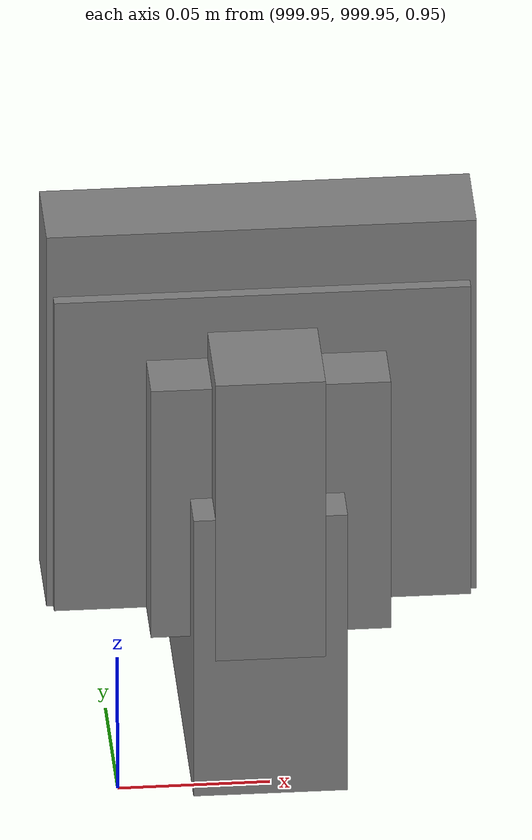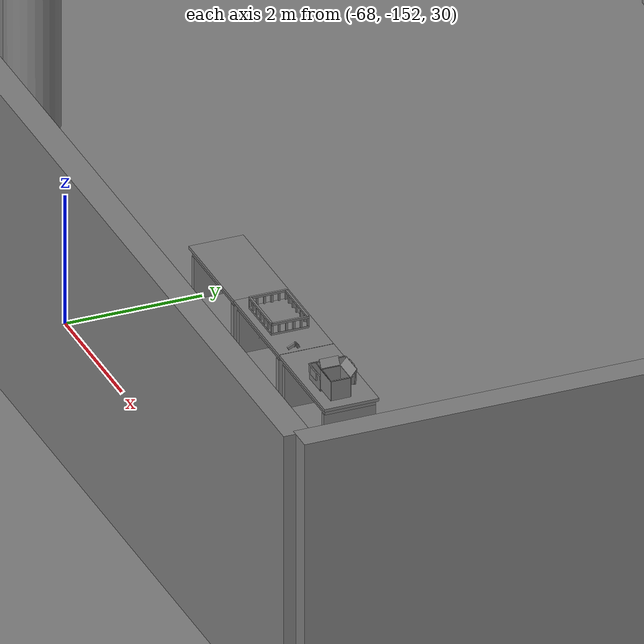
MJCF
<mujoco>
    <option gravity="0.000000000 0.000000000 -9.810000420" timestep="0.0049999999" integrator="implicitfast" density="1.225" viscosity="1.8000001e-05" noslip_iterations="10" iterations="100" sdf_iterations="50">
        <flag multiccd="disable"/>
    </option>
    <size memory="1000M"/>
    <compiler coordinate="local"/>
    <worldbody>
        <light cutoff="30" pos="0 1 1" dir="0 -1 -2"/>
        <light cutoff="30" pos="0 -1 1" dir="0 1 -2"/>
        <body pos="1000.000000000 1000.000000000 1.000000000" euler="0.000000000 0.000000000 180.000000000" name="openloong_gripper_2f85_fix_base_usda_battery_01">
            <geom contype="1" conaffinity="1" density="1000" type="box" material="" rgba="0.500000000 0.500000000 0.500000000 1.000000000" solimp="0.899999976 0.949999988 0.001000000" friction="1.000000000 0.005000000 0.000100000" solref="0.020000000 1.000000000" margin="0" condim="3" group="0" pos="-0.011123657 -0.041940309 0.101691343" quat="1.000000000 0.000000000 0.000000000 0.000000000" size="0.010800000 0.003375000 0.004725000" name="openloong_gripper_2f85_fix_base_usda_geom_8310D1EA_5F7A_4CA7_814D_4BF52CF1A010"/>
            <geom contype="1" conaffinity="1" density="1000" type="box" material="" rgba="0.500000000 0.500000000 0.500000000 1.000000000" solimp="0.899999976 0.949999988 0.001000000" friction="1.000000000 0.005000000 0.000100000" solref="0.020000000 1.000000000" margin="0" condim="3" group="0" pos="-0.010876465 -0.044247437 0.047066893" quat="0.998702705 -0.050920475 0.000000000 0.000000000" size="0.009450001 0.002700000 0.024975000" name="openloong_gripper_2f85_fix_base_usda_geom_CE0A56D7_CED4_4ECF_90CA_69B053F724AF"/>
            <geom contype="1" conaffinity="1" density="1000" type="box" material="" rgba="0.500000000 0.500000000 0.500000000 1.000000000" solimp="0.899999976 0.949999988 0.001000000" friction="1.000000000 0.005000000 0.000100000" solref="0.020000000 1.000000000" margin="0" condim="3" group="0" pos="-0.001235962 -0.000659180 0.047381196" quat="1.000000000 0.000000000 0.000000000 0.000000000" size="0.039420001 0.039150000 0.047250003" name="openloong_gripper_2f85_fix_base_usda_geom_DE2F8BA9_1199_43EC_9CC4_E1C64FB04D60"/>
            <geom contype="1" conaffinity="1" density="1000" type="box" material="" rgba="0.500000000 0.500000000 0.500000000 1.000000000" solimp="0.899999976 0.949999988 0.001000000" friction="1.000000000 0.005000000 0.000100000" solref="0.020000000 1.000000000" margin="0" condim="3" group="0" pos="-0.010876465 -0.039138794 0.009851727" quat="1.000000000 0.000000000 0.000000000 0.000000000" size="0.009450001 0.010800000 0.013500000" name="openloong_gripper_2f85_fix_base_usda_geom_442BF403_352C_4380_B2E9_A6FD41499C6E"/>
            <geom contype="1" conaffinity="1" density="1000" type="box" material="" rgba="0.500000000 0.500000000 0.500000000 1.000000000" solimp="0.899999976 0.949999988 0.001000000" friction="1.000000000 0.005000000 0.000100000" solref="0.020000000 1.000000000" margin="0" condim="3" group="0" pos="-0.010876465 -0.041528322 0.071508206" quat="1.000000000 0.000000000 0.000000000 0.000000000" size="0.009450001 0.002700000 0.027000001" name="openloong_gripper_2f85_fix_base_usda_geom_55117E8B_0726_4FEE_AAF9_C39772324657"/>
            <freejoint name="openloong_gripper_2f85_fix_base_usda_battery_01_joint"/>
            <site size="0.005000000 0.005000000 0.005000000" rgba="0.500000000 0.500000000 0.500000000 1.000000000" pos="0.000000000 0.000000000 0.000000000" quat="0.999961913 0.008726500 0.000000000 0.000000000" group="0" type="sphere" name="openloong_gripper_2f85_fix_base_usda_battery_01site"/>
        </body>
        <body pos="1000.000000000 1000.000000000 1.000000000" euler="0.000000000 0.000000000 180.000000000" name="openloong_gripper_2f85_fix_base_usda_wifi_box">
            <geom contype="1" conaffinity="1" density="1000" type="box" material="" rgba="0.500000000 0.500000000 0.500000000 1.000000000" solimp="0.899999976 0.949999988 0.001000000" friction="1.000000000 0.005000000 0.000100000" solref="0.020000000 1.000000000" margin="0" condim="3" group="0" pos="0.000000000 0.000000000 0.058978677" quat="0.000000000 0.000000047 0.000000000 1.000000000" size="0.068499997 0.018999999 0.059000000" name="openloong_gripper_2f85_fix_base_usda_geom_082F673C_8EC8_4349_935C_BE8ADB4020D7"/>
            <freejoint name="openloong_gripper_2f85_fix_base_usda_wifi_box_joint"/>
            <site size="0.005000000 0.005000000 0.005000000" rgba="0.500000000 0.500000000 0.500000000 1.000000000" pos="0.000000000 0.000000000 0.000000000" quat="0.999961913 0.008726500 0.000000000 0.000000000" group="0" type="sphere" name="openloong_gripper_2f85_fix_base_usda_wifi_boxsite"/>
        </body>
        <body pos="1000.000000000 1000.000000000 1.000000000" euler="0.000000000 0.000000000 180.000000000" name="openloong_gripper_2f85_fix_base_usda_cpu_fan">
            <geom contype="1" conaffinity="1" density="1000" type="box" material="" rgba="0.500000000 0.500000000 0.500000000 1.000000000" solimp="0.899999976 0.949999988 0.001000000" friction="1.000000000 0.005000000 0.000100000" solref="0.020000000 1.000000000" margin="0" condim="3" group="0" pos="0.000000000 0.000000000 0.070034981" quat="0.000000000 0.000000000 0.000000000 1.000000000" size="0.070700005 0.014699999 0.070700005" name="openloong_gripper_2f85_fix_base_usda_geom_2971735C_4DC4_4752_B293_D9CF7BBCE183"/>
            <freejoint name="openloong_gripper_2f85_fix_base_usda_cpu_fan_joint"/>
            <site size="0.005000000 0.005000000 0.005000000" rgba="0.500000000 0.500000000 0.500000000 1.000000000" pos="0.000000000 0.000000000 0.000000000" quat="0.999961913 0.008726535 0.000000000 0.000000000" group="0" type="sphere" name="openloong_gripper_2f85_fix_base_usda_cpu_fancsite"/>
        </body>
        <body pos="1000.000000000 1000.000000000 1.000000000" euler="0.000011953 0.000005123 -179.999984741" name="openloong_gripper_2f85_fix_base_usda_intel_box">
            <geom contype="1" conaffinity="1" density="1000" type="box" material="" rgba="0.500000000 0.500000000 0.500000000 1.000000000" solimp="0.899999976 0.949999988 0.001000000" friction="1.000000000 0.005000000 0.000100000" solref="0.020000000 1.000000000" margin="0" condim="3" group="0" pos="0.000000000 -0.000067139 0.000082284" quat="0.707106709 0.000000225 0.000000253 0.707106650" size="0.052800003 0.025300000 0.052800003" name="openloong_gripper_2f85_fix_base_usda_geom_24254941_FDC8_454D_96C4_BE9434CD022B"/>
            <freejoint name="openloong_gripper_2f85_fix_base_usda_intel_box_joint"/>
            <site size="0.005000000 0.005000000 0.005000000" rgba="0.500000000 0.500000000 0.500000000 1.000000000" pos="0.000000000 0.000000000 0.000000000" quat="0.999961913 0.008726500 0.000000000 0.000000000" group="0" type="sphere" name="openloong_gripper_2f85_fix_base_usda_intel_boxsite"/>
        </body>
        <body pos="1000.000000000 999.999938965 1.000000000" euler="0.000000000 0.000000000 180.000000000" name="openloong_gripper_2f85_fix_base_usda_intelcore_i5">
            <geom contype="1" conaffinity="1" density="1000" type="box" material="" rgba="0.500000000 0.500000000 0.500000000 1.000000000" solimp="0.899999976 0.949999988 0.001000000" friction="1.000000000 0.005000000 0.000100000" solref="0.020000000 1.000000000" margin="0" condim="3" group="0" pos="0.000000000 0.000000000 0.051722717" quat="0.707106709 0.000000000 0.000000000 -0.707106769" size="0.052800000 0.018080002 0.052800000" name="openloong_gripper_2f85_fix_base_usda_geom_FC5D2B3D_2211_4716_ADE6_1C7AFD181265"/>
            <freejoint name="openloong_gripper_2f85_fix_base_usda_intelcore_i5_joint"/>
            <site size="0.005000000 0.005000000 0.005000000" rgba="0.500000000 0.500000000 0.500000000 1.000000000" pos="0.000000000 0.000000000 0.000000000" quat="0.999961913 0.008726534 0.000000000 0.000000000" group="0" type="sphere" name="openloong_gripper_2f85_fix_base_usda_intelcore_i5site"/>
        </body>
        <body pos="-65.985092163 -149.400909424 31.166324615" euler="131.565917969 -8.824352264 -37.347194672" mocap="true" name="spotlight1_SpotLight"/>
        <body pos="-66.305793762 -149.497909546 31.171434402" euler="158.242446899 10.171292305 21.629802704" mocap="true" name="spotlight2_SpotLight"/>
        <body pos="-66.229972839 -149.243255615 31.167564392" euler="98.439453125 27.611331940 -151.180847168" mocap="true" name="spotlight4_SpotLight"/>
        <body pos="-64.866622925 -149.383972168 30.183746338" euler="89.999984741 89.999946594 0.000000000" name="openloong_gripper_2f85_fix_base_usda_bluebox_01">
            <geom contype="1" conaffinity="1" density="1000" type="box" material="" rgba="0.500000000 0.500000000 0.500000000 1.000000000" solimp="0.899999976 0.949999988 0.001000000" friction="1.000000000 0.005000000 0.000100000" solref="0.020000000 1.000000000" margin="0" condim="3" group="0" pos="0.276580811 0.187225342 0.000068665" quat="0.707106948 0.000077471 0.707106352 0.000077486" size="0.100000001 0.057999998 0.010000000" name="openloong_gripper_2f85_fix_base_usda_geom_A0B59DB7_E46A_46F9_907F_973F4C6CD3CA"/>
            <geom contype="1" conaffinity="1" density="1000" type="box" material="" rgba="0.500000000 0.500000000 0.500000000 1.000000000" solimp="0.899999976 0.949999988 0.001000000" friction="1.000000000 0.005000000 0.000100000" solref="0.020000000 1.000000000" margin="0" condim="3" group="0" pos="0.000000000 0.002883911 0.000000000" quat="0.999999881 0.000000000 0.000000000 0.000000000" size="0.254000008 0.003000000 0.172000006" name="openloong_gripper_2f85_fix_base_usda_geom_7597EB3A_13A8_45A5_BB15_F5B7E8E3C763"/>
            <geom contype="1" conaffinity="1" density="1000" type="box" material="" rgba="0.500000000 0.500000000 0.500000000 1.000000000" solimp="0.899999976 0.949999988 0.001000000" friction="1.000000000 0.005000000 0.000100000" solref="0.020000000 1.000000000" margin="0" condim="3" group="0" pos="0.000000000 0.124874115 0.173484802" quat="0.999796331 0.020176515 -0.000000015 0.000000030" size="0.259999990 0.119999997 0.007000000" name="openloong_gripper_2f85_fix_base_usda_geom_0B521060_FE3F_4BF8_91C1_7369DA748C22"/>
            <geom contype="1" conaffinity="1" density="1000" type="box" material="" rgba="0.500000000 0.500000000 0.500000000 1.000000000" solimp="0.899999976 0.949999988 0.001000000" friction="1.000000000 0.005000000 0.000100000" solref="0.020000000 1.000000000" margin="0" condim="3" group="0" pos="0.000000000 0.124874115 -0.173469543" quat="0.999796331 -0.020176545 -0.000000015 0.000000000" size="0.259999990 0.119999997 0.007000000" name="openloong_gripper_2f85_fix_base_usda_geom_F9E77283_8340_4877_B944_70E57DC7D546"/>
            <geom contype="1" conaffinity="1" density="1000" type="box" material="" rgba="0.500000000 0.500000000 0.500000000 1.000000000" solimp="0.899999976 0.949999988 0.001000000" friction="1.000000000 0.005000000 0.000100000" solref="0.020000000 1.000000000" margin="0" condim="3" group="0" pos="0.000000000 0.214008331 0.188980103" quat="0.999912977 0.013176724 0.000000015 0.000000000" size="0.259999990 0.029999999 0.012500000" name="openloong_gripper_2f85_fix_base_usda_geom_020DAB4F_BAC5_4E48_8AC8_B953C36EAE5C"/>
            <geom contype="1" conaffinity="1" density="1000" type="box" material="" rgba="0.500000000 0.500000000 0.500000000 1.000000000" solimp="0.899999976 0.949999988 0.001000000" friction="1.000000000 0.005000000 0.000100000" solref="0.020000000 1.000000000" margin="0" condim="3" group="0" pos="-0.258361816 0.125289917 0.001876831" quat="0.702796936 -0.020792112 0.710783124 0.020769298" size="0.189999998 0.119999997 0.009000000" name="openloong_gripper_2f85_fix_base_usda_geom_CC5A3FC7_32FA_4F87_A4B1_C7CFD05909B7"/>
            <geom contype="1" conaffinity="1" density="1000" type="box" material="" rgba="0.500000000 0.500000000 0.500000000 1.000000000" solimp="0.899999976 0.949999988 0.001000000" friction="1.000000000 0.005000000 0.000100000" solref="0.020000000 1.000000000" margin="0" condim="3" group="0" pos="0.000000000 0.214008331 -0.188980103" quat="0.999912977 -0.013176769 0.000000030 0.000000015" size="0.259999990 0.029999999 0.012500000" name="openloong_gripper_2f85_fix_base_usda_geom_F5AB7CE4_C867_4DC8_A562_0A2A093CC92D"/>
            <geom contype="1" conaffinity="1" density="1000" type="box" material="" rgba="0.500000000 0.500000000 0.500000000 1.000000000" solimp="0.899999976 0.949999988 0.001000000" friction="1.000000000 0.005000000 0.000100000" solref="0.020000000 1.000000000" margin="0" condim="3" group="0" pos="-0.276611328 0.187225342 0.000068665" quat="0.707106650 0.000077441 0.707106709 0.000077456" size="0.100000001 0.057999998 0.010000000" name="openloong_gripper_2f85_fix_base_usda_geom_4761E1F0_61D7_4B6D_9B59_8FC623F61A87"/>
            <geom contype="1" conaffinity="1" density="1000" type="box" material="" rgba="0.500000000 0.500000000 0.500000000 1.000000000" solimp="0.899999976 0.949999988 0.001000000" friction="1.000000000 0.005000000 0.000100000" solref="0.020000000 1.000000000" margin="0" condim="3" group="0" pos="0.258331299 0.125289917 0.001876831" quat="0.702851415 0.018856421 0.710823774 -0.019329369" size="0.189999998 0.119999997 0.009000000" name="openloong_gripper_2f85_fix_base_usda_geom_7B603C10_8D34_4BA3_81FA_66ABDB9933DF"/>
            <freejoint name="openloong_gripper_2f85_fix_base_usda_bluebox_01_joint"/>
            <site size="0.005000000 0.005000000 0.005000000" rgba="0.500000000 0.500000000 0.500000000 1.000000000" pos="0.000000000 0.000000000 0.000000000" quat="0.999961913 0.008726534 0.000000000 0.000000000" group="0" type="sphere" name="openloong_gripper_2f85_fix_base_usda_bluebox_01site"/>
        </body>
        <body pos="-64.496299744 -149.491867065 30.235729218" euler="0.000000000 0.000000000 89.999946594" name="openloong_gripper_2f85_fix_base_usda_cardboardbox_01">
            <geom contype="1" conaffinity="1" density="1000" type="box" material="" rgba="0.500000000 0.500000000 0.500000000 1.000000000" solimp="0.899999976 0.949999988 0.001000000" friction="1.000000000 0.005000000 0.000100000" solref="0.020000000 1.000000000" margin="0" condim="3" group="0" pos="-0.003166199 -0.004086494 0.005052090" quat="1.000000000 0.000000000 0.000000000 0.000000000" size="0.142499998 0.177500010 0.005000000" name="openloong_gripper_2f85_fix_base_usda_geom_FF353D03_A7B4_4127_8211_E1C3B74AB68F"/>
            <geom contype="1" conaffinity="1" density="1000" type="box" material="" rgba="0.500000000 0.500000000 0.500000000 1.000000000" solimp="0.899999976 0.949999988 0.001000000" friction="1.000000000 0.005000000 0.000100000" solref="0.020000000 1.000000000" margin="0" condim="3" group="0" pos="-0.003166199 0.170316696 0.150570869" quat="1.000000000 0.000000000 0.000000000 0.000000000" size="0.142499998 0.005000000 0.149999991" name="openloong_gripper_2f85_fix_base_usda_geom_B9122CB7_B12B_45BB_A868_E5D97624B831"/>
            <geom contype="1" conaffinity="1" density="1000" type="box" material="" rgba="0.500000000 0.500000000 0.500000000 1.000000000" solimp="0.899999976 0.949999988 0.001000000" friction="1.000000000 0.005000000 0.000100000" solref="0.020000000 1.000000000" margin="0" condim="3" group="0" pos="-0.147399902 -0.005307198 0.150570869" quat="1.000000000 0.000000000 0.000000000 0.000000000" size="0.005000000 0.177500010 0.149999991" name="openloong_gripper_2f85_fix_base_usda_geom_F3C4D247_E42A_4EEC_9724_E7D34FF4948B"/>
            <geom contype="1" conaffinity="1" density="1000" type="box" material="" rgba="0.500000000 0.500000000 0.500000000 1.000000000" solimp="0.899999976 0.949999988 0.001000000" friction="1.000000000 0.005000000 0.000100000" solref="0.020000000 1.000000000" margin="0" condim="3" group="0" pos="0.140275955 -0.005307198 0.150570869" quat="1.000000000 0.000000000 0.000000000 0.000000000" size="0.005000000 0.177500010 0.149999991" name="openloong_gripper_2f85_fix_base_usda_geom_0C658A38_72B3_4821_A296_BB9FDA99F64B"/>
            <geom contype="1" conaffinity="1" density="1000" type="box" material="" rgba="0.500000000 0.500000000 0.500000000 1.000000000" solimp="0.899999976 0.949999988 0.001000000" friction="1.000000000 0.005000000 0.000100000" solref="0.020000000 1.000000000" margin="0" condim="3" group="0" pos="-0.003166199 -0.181550980 0.150570869" quat="1.000000000 0.000000000 0.000000000 0.000000000" size="0.142499998 0.005000000 0.149999991" name="openloong_gripper_2f85_fix_base_usda_geom_CE938E44_7905_4C35_85F8_8781FAC55197"/>
            <freejoint name="openloong_gripper_2f85_fix_base_usda_cardboardbox_01_joint"/>
            <site size="0.005000000 0.005000000 0.005000000" rgba="0.500000000 0.500000000 0.500000000 1.000000000" pos="0.000000000 0.000000000 0.000000000" quat="0.999961913 0.008726535 0.000000000 0.000000000" group="0" type="sphere" name="openloong_gripper_2f85_fix_base_usda_site_C697AC9B_088D_4BC5_9EF8_FEEECAA36765"/>
            <body pos="0.139160156 -0.004048347 0.301930904" euler="-179.999954224 49.383502960 179.999954224" name="openloong_gripper_2f85_fix_base_usda_A1_006">
                <geom contype="1" conaffinity="1" density="1000" type="box" material="" rgba="0.500000000 0.500000000 0.500000000 1.000000000" solimp="0.899999976 0.949999988 0.001000000" friction="1.000000000 0.005000000 0.000100000" solref="0.020000000 1.000000000" margin="0" condim="3" group="0" pos="-0.071587563 0.000009537 0.001745224" quat="0.999999881 0.000000000 0.000000000 0.000000000" size="0.071249999 0.179999992 0.002500000" name="openloong_gripper_2f85_fix_base_usda_geom_A21EC263_E310_43B6_ABCD_66AF36B8EF5E"/>
                <joint armature="0" stiffness="0.07" damping="0.0099999998" axis="0.000000 1.000000 0.000000" type="hinge" name="openloong_gripper_2f85_fix_base_usda_A1_006"/>
            </body>
            <body pos="-0.145902634 -0.004086494 0.301938057" euler="-180.000000000 -60.000011444 -180.000000000" name="openloong_gripper_2f85_fix_base_usda_A2_006">
                <geom contype="1" conaffinity="1" density="1000" type="box" material="" rgba="0.500000000 0.500000000 0.500000000 1.000000000" solimp="0.899999976 0.949999988 0.001000000" friction="1.000000000 0.005000000 0.000100000" solref="0.020000000 1.000000000" margin="0" condim="3" group="0" pos="0.071268082 0.000009537 0.002717972" quat="0.000002921 0.000000000 -0.000000030 0.999999881" size="0.071249999 0.179999992 0.002500000" name="openloong_gripper_2f85_fix_base_usda_geom_59321EFD_FE0F_4E82_BFFA_5E6642722FCE"/>
                <joint armature="0" stiffness="0.07" damping="0.0099999998" axis="0.000000 1.000000 0.000000" type="hinge" name="openloong_gripper_2f85_fix_base_usda_A2_006"/>
            </body>
            <body pos="-0.003385544 0.175991058 0.301930904" euler="-125.858116150 -0.000004561 0.000002331" name="openloong_gripper_2f85_fix_base_usda_B2_006">
                <geom contype="1" conaffinity="1" density="1000" type="box" material="" rgba="0.500000000 0.500000000 0.500000000 1.000000000" solimp="0.899999976 0.949999988 0.001000000" friction="1.000000000 0.005000000 0.000100000" solref="0.020000000 1.000000000" margin="0" condim="3" group="0" pos="0.000009537 -0.070939064 -0.002470016" quat="0.999614120 0.027776197 -0.000000015 0.000000030" size="0.137500003 0.064999998 0.005000000" name="openloong_gripper_2f85_fix_base_usda_geom_6236EE74_6C4F_4CB9_A5DD_D4AB5EFE78C4"/>
                <joint armature="0" stiffness="0.07" damping="0.0099999998" axis="1.000000 0.000000 0.000000" type="hinge" name="openloong_gripper_2f85_fix_base_usda_B2_006"/>
            </body>
            <body pos="-0.003385544 -0.184140205 0.301938057" euler="147.805557251 0.000000000 0.000000000" name="openloong_gripper_2f85_fix_base_usda_B1_006">
                <geom contype="1" conaffinity="1" density="1000" type="box" material="" rgba="0.500000000 0.500000000 0.500000000 1.000000000" solimp="0.899999976 0.949999988 0.001000000" friction="1.000000000 0.005000000 0.000100000" solref="0.020000000 1.000000000" margin="0" condim="3" group="0" pos="-0.000028610 0.070202351 -0.002703667" quat="0.999614179 -0.027776167 0.000000000 0.000000000" size="0.137500003 0.064999998 0.005000000" name="openloong_gripper_2f85_fix_base_usda_geom_CFE12B1A_694D_4152_8886_72BAEB0B733F"/>
                <joint armature="0" stiffness="0.07" damping="0.0099999998" axis="1.000000 0.000000 0.000000" type="hinge" name="openloong_gripper_2f85_fix_base_usda_B1_006"/>
            </body>
        </body>
        <body pos="-65.882858276 -149.481979370 30.229999542" euler="-64.487716675 0.000000000 0.000000000" name="openloong_gripper_2f85_fix_base_usda_Barcode">
            <geom contype="1" conaffinity="1" density="1000" type="box" material="" rgba="0.500000000 0.500000000 0.500000000 1.000000000" solimp="0.899999976 0.949999988 0.001000000" friction="1.000000000 0.005000000 0.000100000" solref="0.020000000 1.000000000" margin="0" condim="3" group="0" pos="0.000000000 0.013038635 0.001419067" quat="0.000000000 0.000000000 0.000000000 1.000000119" size="0.034000002 0.010000000 0.017999999" name="openloong_gripper_2f85_fix_base_usda_geom_61761CC6_3ED5_495D_87D6_D2F087AA0B0B"/>
            <geom contype="1" conaffinity="1" density="1000" type="box" material="" rgba="0.500000000 0.500000000 0.500000000 1.000000000" solimp="0.899999976 0.949999988 0.001000000" friction="1.000000000 0.005000000 0.000100000" solref="0.020000000 1.000000000" margin="0" condim="3" group="0" pos="0.000000000 -0.035301208 -0.007095337" quat="0.000000000 0.000000000 -0.043619365 0.999048233" size="0.028999999 0.010000000 0.020000000" name="openloong_gripper_2f85_fix_base_usda_geom_34EFC0BD_3D7A_4FE9_B48A_81F7848121BE"/>
            <geom contype="1" conaffinity="1" density="1000" type="box" material="" rgba="0.500000000 0.500000000 0.500000000 1.000000000" solimp="0.899999976 0.949999988 0.001000000" friction="1.000000000 0.005000000 0.000100000" solref="0.020000000 1.000000000" margin="0" condim="3" group="0" pos="0.000000000 -0.043411255 -0.011749268" quat="0.922262907 0.386563420 0.000000000 0.000000000" size="0.026000001 0.010000000 0.020000000" name="openloong_gripper_2f85_fix_base_usda_geom_2778B848_E696_478C_9C1E_0DD53ED57536"/>
            <geom contype="1" conaffinity="1" density="1000" type="box" material="" rgba="0.500000000 0.500000000 0.500000000 1.000000000" solimp="0.899999976 0.949999988 0.001000000" friction="1.000000000 0.005000000 0.000100000" solref="0.020000000 1.000000000" margin="0" condim="3" group="0" pos="0.000000000 -0.016967773 -0.031860352" quat="0.000000000 0.000000000 0.000000000 1.000000119" size="0.008000000 0.010000000 0.013000000" name="openloong_gripper_2f85_fix_base_usda_geom_0415951A_CF2E_424A_A778_5B107082D630"/>
            <geom contype="1" conaffinity="1" density="1000" type="box" material="" rgba="0.500000000 0.500000000 0.500000000 1.000000000" solimp="0.899999976 0.949999988 0.001000000" friction="1.000000000 0.005000000 0.000100000" solref="0.020000000 1.000000000" margin="0" condim="3" group="0" pos="0.000000000 -0.001869202 0.000312805" quat="0.953716993 0.300705761 0.000000000 0.000000000" size="0.032000002 0.010000000 0.018999999" name="openloong_gripper_2f85_fix_base_usda_geom_D8869667_EEED_4EF8_882C_9566187D0320"/>
            <geom contype="1" conaffinity="1" density="1000" type="box" material="" rgba="0.500000000 0.500000000 0.500000000 1.000000000" solimp="0.899999976 0.949999988 0.001000000" friction="1.000000000 0.005000000 0.000100000" solref="0.020000000 1.000000000" margin="0" condim="3" group="0" pos="0.000000000 -0.019531250 -0.003173828" quat="0.953716993 0.300705761 0.000000000 0.000000000" size="0.030999999 0.010000000 0.020000000" name="openloong_gripper_2f85_fix_base_usda_geom_6BF328EC_2D3B_4D9B_A4BB_0C1761BCD87A"/>
            <geom contype="1" conaffinity="1" density="1000" type="box" material="" rgba="0.500000000 0.500000000 0.500000000 1.000000000" solimp="0.899999976 0.949999988 0.001000000" friction="1.000000000 0.005000000 0.000100000" solref="0.020000000 1.000000000" margin="0" condim="3" group="0" pos="0.000000000 -0.035301208 -0.007095337" quat="0.953716993 0.300705761 0.000000000 0.000000000" size="0.028999999 0.010000000 0.020000000" name="openloong_gripper_2f85_fix_base_usda_geom_2DA90F93_839D_4781_B0D1_58422C210964"/>
            <geom contype="1" conaffinity="1" density="1000" type="box" material="" rgba="0.500000000 0.500000000 0.500000000 1.000000000" solimp="0.899999976 0.949999988 0.001000000" friction="1.000000000 0.005000000 0.000100000" solref="0.020000000 1.000000000" margin="0" condim="3" group="0" pos="0.000000000 -0.042617798 -0.071121216" quat="0.000000000 0.000000000 0.000000000 1.000000119" size="0.013000000 0.021000000 0.059999999" name="openloong_gripper_2f85_fix_base_usda_geom_18750439_BE5D_44CE_B73B_A4425E9FF3FA"/>
            <freejoint name="openloong_gripper_2f85_fix_base_usda_Barcode_joint"/>
            <site size="0.005000000 0.005000000 0.005000000" rgba="0.500000000 0.500000000 0.500000000 1.000000000" pos="0.000000000 0.000000000 0.000000000" quat="1.000000000 0.000000000 0.000000000 0.000000000" group="0" type="sphere" name="openloong_gripper_2f85_fix_base_usda_Barcode_site"/>
        </body>
        <body pos="-66.745018005 -149.392349243 30.184000015" euler="0.000000000 0.000000000 89.999946594" name="[22330750179281]_Basket_01">
            <geom contype="1" conaffinity="1" density="1000" type="box" material="" rgba="0.500000000 0.500000000 0.500000000 1.000000000" solimp="0.899999976 0.949999988 0.001000000" friction="1.000000000 0.005000000 0.000100000" solref="0.020000000 1.000000000" margin="0" condim="3" group="0" pos="-0.052425385 0.389207840 0.089787483" quat="0.707107008 0.000000000 0.000000000 0.707106411" size="0.014249999 0.014249999 0.059999999" name="[22330750179281]_geom_55444E74_560A_450E_A9E2_A7DC31A04E5E"/>
            <geom contype="1" conaffinity="1" density="1000" type="box" material="" rgba="0.500000000 0.500000000 0.500000000 1.000000000" solimp="0.899999976 0.949999988 0.001000000" friction="1.000000000 0.005000000 0.000100000" solref="0.020000000 1.000000000" margin="0" condim="3" group="0" pos="0.264015198 -0.133043289 0.089787483" quat="0.707107008 0.000000000 0.000000000 0.707106411" size="0.014249999 0.014249999 0.059999999" name="[22330750179281]_geom_360C8858_49CB_4CE3_B7AD_53125BB02A7C"/>
            <geom contype="1" conaffinity="1" density="1000" type="box" material="" rgba="0.500000000 0.500000000 0.500000000 1.000000000" solimp="0.899999976 0.949999988 0.001000000" friction="1.000000000 0.005000000 0.000100000" solref="0.020000000 1.000000000" margin="0" condim="3" group="0" pos="-0.264015198 -0.265548706 0.089793205" quat="0.707107008 0.000000000 0.000000000 0.707106411" size="0.014249999 0.014249999 0.059999999" name="[22330750179281]_geom_BB9C2002_9C20_4B6E_94EE_9E286DEC8602"/>
            <geom contype="1" conaffinity="1" density="1000" type="box" material="" rgba="0.500000000 0.500000000 0.500000000 1.000000000" solimp="0.899999976 0.949999988 0.001000000" friction="1.000000000 0.005000000 0.000100000" solref="0.020000000 1.000000000" margin="0" condim="3" group="0" pos="-0.160263062 -0.389322281 0.089793205" quat="0.707107008 0.000000000 0.000000000 0.707106411" size="0.014249999 0.014249999 0.059999999" name="[22330750179281]_geom_AD1064A5_1CEB_487A_AE2A_64930B8E6B25"/>
            <geom contype="1" conaffinity="1" density="1000" type="box" material="" rgba="0.500000000 0.500000000 0.500000000 1.000000000" solimp="0.899999976 0.949999988 0.001000000" friction="1.000000000 0.005000000 0.000100000" solref="0.020000000 1.000000000" margin="0" condim="3" group="0" pos="0.162265778 -0.389322281 0.089787483" quat="0.707107008 0.000000000 0.000000000 0.707106411" size="0.014249999 0.014249999 0.059999999" name="[22330750179281]_geom_56C91DCF_55A5_4D85_9489_51190DFD4ED3"/>
            <geom contype="1" conaffinity="1" density="1000" type="box" material="" rgba="0.500000000 0.500000000 0.500000000 1.000000000" solimp="0.899999976 0.949999988 0.001000000" friction="1.000000000 0.005000000 0.000100000" solref="0.020000000 1.000000000" margin="0" condim="3" group="0" pos="0.264015198 0.389207840 0.089787483" quat="0.707107008 0.000000000 0.000000000 0.707106411" size="0.014249999 0.014249999 0.059999999" name="[22330750179281]_geom_CA988DA3_DAA9_4704_9BDF_E2012771F816"/>
            <geom contype="1" conaffinity="1" density="1000" type="box" material="" rgba="0.500000000 0.500000000 0.500000000 1.000000000" solimp="0.899999976 0.949999988 0.001000000" friction="1.000000000 0.005000000 0.000100000" solref="0.020000000 1.000000000" margin="0" condim="3" group="0" pos="-0.264015198 -0.133043289 0.089793205" quat="0.707107008 0.000000000 0.000000000 0.707106411" size="0.014249999 0.014249999 0.059999999" name="[22330750179281]_geom_757FF82C_1374_41E4_A9B0_32D2B3470B51"/>
            <geom contype="1" conaffinity="1" density="1000" type="box" material="" rgba="0.500000000 0.500000000 0.500000000 1.000000000" solimp="0.899999976 0.949999988 0.001000000" friction="1.000000000 0.005000000 0.000100000" solref="0.020000000 1.000000000" margin="0" condim="3" group="0" pos="-0.264026642 0.269256592 0.089793205" quat="0.707107008 0.000000000 0.000000000 0.707106411" size="0.014249999 0.014249999 0.059999999" name="[22330750179281]_geom_2889E418_0234_4B3D_972F_C80B5AB995AF"/>
            <geom contype="1" conaffinity="1" density="1000" type="box" material="" rgba="0.500000000 0.500000000 0.500000000 1.000000000" solimp="0.899999976 0.949999988 0.001000000" friction="1.000000000 0.005000000 0.000100000" solref="0.020000000 1.000000000" margin="0" condim="3" group="0" pos="0.054462433 0.389207840 0.089787483" quat="0.707107008 0.000000000 0.000000000 0.707106411" size="0.014249999 0.014249999 0.059999999" name="[22330750179281]_geom_E9C7D38A_F4BE_479A_A90F_8E9750D8B436"/>
            <geom contype="1" conaffinity="1" density="1000" type="box" material="" rgba="0.500000000 0.500000000 0.500000000 1.000000000" solimp="0.899999976 0.949999988 0.001000000" friction="1.000000000 0.005000000 0.000100000" solref="0.020000000 1.000000000" margin="0" condim="3" group="0" pos="0.054462433 -0.389322281 0.089787483" quat="0.707107008 0.000000000 0.000000000 0.707106411" size="0.014249999 0.014249999 0.059999999" name="[22330750179281]_geom_944A46CA_9E46_4BE4_825A_3D41C0148528"/>
            <geom contype="1" conaffinity="1" density="1000" type="box" material="" rgba="0.500000000 0.500000000 0.500000000 1.000000000" solimp="0.899999976 0.949999988 0.001000000" friction="1.000000000 0.005000000 0.000100000" solref="0.020000000 1.000000000" margin="0" condim="3" group="0" pos="0.264015198 0.269256592 0.089793205" quat="0.707107008 0.000000000 0.000000000 0.707106411" size="0.014249999 0.014249999 0.059999999" name="[22330750179281]_geom_F304C8CB_E9C1_4E0D_9F14_8CC57F787675"/>
            <geom contype="1" conaffinity="1" density="1000" type="box" material="" rgba="0.500000000 0.500000000 0.500000000 1.000000000" solimp="0.899999976 0.949999988 0.001000000" friction="1.000000000 0.005000000 0.000100000" solref="0.020000000 1.000000000" margin="0" condim="3" group="0" pos="0.264015198 -0.389322281 0.089787483" quat="0.707107008 0.000000000 0.000000000 0.707106411" size="0.014249999 0.014249999 0.059999999" name="[22330750179281]_geom_0C8FD033_8491_4FB0_8CDB_D37ADC3E151D"/>
            <geom contype="1" conaffinity="1" density="1000" type="box" material="" rgba="0.500000000 0.500000000 0.500000000 1.000000000" solimp="0.899999976 0.949999988 0.001000000" friction="1.000000000 0.005000000 0.000100000" solref="0.020000000 1.000000000" margin="0" condim="3" group="0" pos="0.000000000 0.000000000 0.015998840" quat="0.707107008 0.000000000 0.000000000 0.707106411" size="0.403499991 0.279000014 0.015750000" name="[22330750179281]_geom_C25FEDE0_42E4_4E77_ACC0_CAEEF69B6356"/>
            <geom contype="1" conaffinity="1" density="1000" type="box" material="" rgba="0.500000000 0.500000000 0.500000000 1.000000000" solimp="0.899999976 0.949999988 0.001000000" friction="1.000000000 0.005000000 0.000100000" solref="0.020000000 1.000000000" margin="0" condim="3" group="0" pos="0.000000000 -0.389476776 0.163619041" quat="0.707107008 0.000000000 0.000000000 0.707106411" size="0.015000000 0.277500004 0.015750000" name="[22330750179281]_geom_7CE0CD5A_1962_48B9_8037_44CA41698751"/>
            <geom contype="1" conaffinity="1" density="1000" type="box" material="" rgba="0.500000000 0.500000000 0.500000000 1.000000000" solimp="0.899999976 0.949999988 0.001000000" friction="1.000000000 0.005000000 0.000100000" solref="0.020000000 1.000000000" margin="0" condim="3" group="0" pos="0.162265778 0.389207840 0.089787483" quat="0.707107008 0.000000000 0.000000000 0.707106411" size="0.014249999 0.014249999 0.059999999" name="[22330750179281]_geom_70564921_40F7_4D27_87BB_36E0C42D4DE9"/>
            <geom contype="1" conaffinity="1" density="1000" type="box" material="" rgba="0.500000000 0.500000000 0.500000000 1.000000000" solimp="0.899999976 0.949999988 0.001000000" friction="1.000000000 0.005000000 0.000100000" solref="0.020000000 1.000000000" margin="0" condim="3" group="0" pos="0.000000000 0.389471054 0.163619041" quat="0.707107008 0.000000000 0.000000000 0.707106411" size="0.015000000 0.277500004 0.015750000" name="[22330750179281]_geom_C0A2F8BD_006F_4F69_B72A_0B122ED17EBB"/>
            <geom contype="1" conaffinity="1" density="1000" type="box" material="" rgba="0.500000000 0.500000000 0.500000000 1.000000000" solimp="0.899999976 0.949999988 0.001000000" friction="1.000000000 0.005000000 0.000100000" solref="0.020000000 1.000000000" margin="0" condim="3" group="0" pos="-0.263511658 0.000000000 0.163619041" quat="0.707107008 0.000000000 0.000000000 0.707106411" size="0.403499991 0.015000000 0.015750000" name="[22330750179281]_geom_E2E86081_D888_46E5_ADE1_CD388C0A1E6D"/>
            <geom contype="1" conaffinity="1" density="1000" type="box" material="" rgba="0.500000000 0.500000000 0.500000000 1.000000000" solimp="0.899999976 0.949999988 0.001000000" friction="1.000000000 0.005000000 0.000100000" solref="0.020000000 1.000000000" margin="0" condim="3" group="0" pos="-0.264015198 0.141334534 0.089793205" quat="0.707107008 0.000000000 0.000000000 0.707106411" size="0.014249999 0.014249999 0.059999999" name="[22330750179281]_geom_37B067C1_4A82_48A0_B507_46CFAFA9C74C"/>
            <geom contype="1" conaffinity="1" density="1000" type="box" material="" rgba="0.500000000 0.500000000 0.500000000 1.000000000" solimp="0.899999976 0.949999988 0.001000000" friction="1.000000000 0.005000000 0.000100000" solref="0.020000000 1.000000000" margin="0" condim="3" group="0" pos="0.264015198 -0.265548706 0.089787483" quat="0.707107008 0.000000000 0.000000000 0.707106411" size="0.014249999 0.014249999 0.059999999" name="[22330750179281]_geom_E66F1CE5_019F_43C6_9CF6_D6A8B3727628"/>
            <geom contype="1" conaffinity="1" density="1000" type="box" material="" rgba="0.500000000 0.500000000 0.500000000 1.000000000" solimp="0.899999976 0.949999988 0.001000000" friction="1.000000000 0.005000000 0.000100000" solref="0.020000000 1.000000000" margin="0" condim="3" group="0" pos="-0.160263062 0.389207840 0.089787483" quat="0.707107008 0.000000000 0.000000000 0.707106411" size="0.014249999 0.014249999 0.059999999" name="[22330750179281]_geom_AC3F2C3D_AA4C_46A8_8171_14BE2DE8250E"/>
            <geom contype="1" conaffinity="1" density="1000" type="box" material="" rgba="0.500000000 0.500000000 0.500000000 1.000000000" solimp="0.899999976 0.949999988 0.001000000" friction="1.000000000 0.005000000 0.000100000" solref="0.020000000 1.000000000" margin="0" condim="3" group="0" pos="-0.052425385 -0.389322281 0.089787483" quat="0.707107008 0.000000000 0.000000000 0.707106411" size="0.014249999 0.014249999 0.059999999" name="[22330750179281]_geom_49AC52B1_9240_4C9D_B4D1_99582BB9F8E0"/>
            <geom contype="1" conaffinity="1" density="1000" type="box" material="" rgba="0.500000000 0.500000000 0.500000000 1.000000000" solimp="0.899999976 0.949999988 0.001000000" friction="1.000000000 0.005000000 0.000100000" solref="0.020000000 1.000000000" margin="0" condim="3" group="0" pos="-0.264026642 -0.389322281 0.089793205" quat="0.707107008 0.000000000 0.000000000 0.707106411" size="0.014249999 0.014249999 0.059999999" name="[22330750179281]_geom_AC79C3FD_960C_4623_919E_72B1ABA9D1A6"/>
            <geom contype="1" conaffinity="1" density="1000" type="box" material="" rgba="0.500000000 0.500000000 0.500000000 1.000000000" solimp="0.899999976 0.949999988 0.001000000" friction="1.000000000 0.005000000 0.000100000" solref="0.020000000 1.000000000" margin="0" condim="3" group="0" pos="0.264015198 0.141334534 0.089787483" quat="0.707107008 0.000000000 0.000000000 0.707106411" size="0.014249999 0.014249999 0.059999999" name="[22330750179281]_geom_43F18188_2139_45F8_B5D4_CED3AF735654"/>
            <geom contype="1" conaffinity="1" density="1000" type="box" material="" rgba="0.500000000 0.500000000 0.500000000 1.000000000" solimp="0.899999976 0.949999988 0.001000000" friction="1.000000000 0.005000000 0.000100000" solref="0.020000000 1.000000000" margin="0" condim="3" group="0" pos="-0.264015198 0.389207840 0.089793205" quat="0.707107008 0.000000000 0.000000000 0.707106411" size="0.014249999 0.014249999 0.059999999" name="[22330750179281]_geom_C8427603_BD41_4794_82FA_A737B7360355"/>
            <geom contype="1" conaffinity="1" density="1000" type="box" material="" rgba="0.500000000 0.500000000 0.500000000 1.000000000" solimp="0.899999976 0.949999988 0.001000000" friction="1.000000000 0.005000000 0.000100000" solref="0.020000000 1.000000000" margin="0" condim="3" group="0" pos="0.264015198 0.004480362 0.089787483" quat="0.707107008 0.000000000 0.000000000 0.707106411" size="0.014249999 0.014249999 0.059999999" name="[22330750179281]_geom_77F8F5FD_A3BA_45CA_9533_1E9CE2D73B25"/>
            <geom contype="1" conaffinity="1" density="1000" type="box" material="" rgba="0.500000000 0.500000000 0.500000000 1.000000000" solimp="0.899999976 0.949999988 0.001000000" friction="1.000000000 0.005000000 0.000100000" solref="0.020000000 1.000000000" margin="0" condim="3" group="0" pos="0.263694763 -0.000011444 0.163619041" quat="0.707107008 0.000000000 0.000000000 0.707106411" size="0.403499991 0.015000000 0.015750000" name="[22330750179281]_geom_6AFAF32E_E5E8_454A_A918_F5FB95B2B4E7"/>
            <geom contype="1" conaffinity="1" density="1000" type="box" material="" rgba="0.500000000 0.500000000 0.500000000 1.000000000" solimp="0.899999976 0.949999988 0.001000000" friction="1.000000000 0.005000000 0.000100000" solref="0.020000000 1.000000000" margin="0" condim="3" group="0" pos="-0.264015198 0.004480362 0.089793205" quat="0.707107008 0.000000000 0.000000000 0.707106411" size="0.014249999 0.014249999 0.059999999" name="[22330750179281]_geom_ED2548C9_31B6_4043_81B0_AD3699E69FC5"/>
            <freejoint name="[22330750179281]_joint_07718FFF_4982_41B0_B59A_E920C62E0663"/>
        </body>
        <body pos="0.000000000 0.000000000 0.000000000" euler="0.000000000 0.000000000 0.000000000" name="Static Objects_Static Objects">
            <geom contype="1" conaffinity="1" density="1000" type="box" material="" rgba="0.500000000 0.500000000 0.500000000 1.000000000" solimp="0.899999976 0.949999988 0.001000000" friction="1.000000000 0.005000000 0.000100000" solref="0.020000000 1.000000000" margin="0" condim="3" group="0" pos="-67.544113159 -149.365814209 29.727830887" quat="0.500000417 0.499999970 0.499999553 0.499999970" size="0.381000012 0.319999993 0.041000001" name="Static Objects_geom_908B195E_5172_481D_881B_7DEF6A8B6B81"/>
            <geom contype="1" conaffinity="1" density="1000" type="box" material="" rgba="0.500000000 0.500000000 0.500000000 1.000000000" solimp="0.899999976 0.949999988 0.001000000" friction="1.000000000 0.005000000 0.000100000" solref="0.020000000 1.000000000" margin="0" condim="3" group="0" pos="-68.239501953 -149.365814209 30.086868286" quat="0.500000417 0.499999970 0.499999553 0.499999970" size="0.370999992 0.039500002 0.745000005" name="Static Objects_geom_93FC23D7_5AA9_487C_94DA_8B92EDC14F1E"/>
            <geom contype="1" conaffinity="1" density="1000" type="box" material="" rgba="0.500000000 0.500000000 0.500000000 1.000000000" solimp="0.899999976 0.949999988 0.001000000" friction="1.000000000 0.005000000 0.000100000" solref="0.020000000 1.000000000" margin="0" condim="3" group="0" pos="-68.239501953 -149.365814209 30.147235870" quat="0.500000417 0.499999970 0.499999553 0.499999970" size="0.400000006 0.022000000 0.800000012" name="Static Objects_geom_6F08EEF0_3937_467B_BA52_37AE640DC22A"/>
            <geom contype="1" conaffinity="1" density="1000" type="box" material="" rgba="0.500000000 0.500000000 0.500000000 1.000000000" solimp="0.899999976 0.949999988 0.001000000" friction="1.000000000 0.005000000 0.000100000" solref="0.020000000 1.000000000" margin="0" condim="3" group="0" pos="-68.934890747 -149.365814209 29.727830887" quat="0.500000417 0.499999970 0.499999553 0.499999970" size="0.381000012 0.319999993 0.041000001" name="Static Objects_geom_CD24F2E9_28AA_403F_BDC6_BA24E8B206FD"/>
            <geom contype="1" conaffinity="1" density="1000" type="box" material="" rgba="0.500000000 0.500000000 0.500000000 1.000000000" solimp="0.899999976 0.949999988 0.001000000" friction="1.000000000 0.005000000 0.000100000" solref="0.020000000 1.000000000" margin="0" condim="3" group="0" pos="-68.239501953 -149.365814209 29.561563492" quat="0.500000417 0.499999970 0.499999553 0.499999970" size="0.020000000 0.022000000 0.660000026" name="Static Objects_geom_E321E05B_A2D4_4DB3_8B35_CAA3E4BB961C"/>
            <geom contype="1" conaffinity="1" density="1000" type="box" material="" rgba="0.500000000 0.500000000 0.500000000 1.000000000" solimp="0.899999976 0.949999988 0.001000000" friction="1.000000000 0.005000000 0.000100000" solref="0.020000000 1.000000000" margin="0" condim="3" group="0" pos="-65.945671082 -149.365814209 29.727830887" quat="0.500000417 0.499999970 0.499999553 0.499999970" size="0.381000012 0.319999993 0.041000001" name="Static Objects_geom_50CDD8AD_1B89_4320_A251_724F5EFA7FD4"/>
            <geom contype="1" conaffinity="1" density="1000" type="box" material="" rgba="0.500000000 0.500000000 0.500000000 1.000000000" solimp="0.899999976 0.949999988 0.001000000" friction="1.000000000 0.005000000 0.000100000" solref="0.020000000 1.000000000" margin="0" condim="3" group="0" pos="-66.641059875 -149.365814209 30.086868286" quat="0.500000417 0.499999970 0.499999553 0.499999970" size="0.370999992 0.039500002 0.745000005" name="Static Objects_geom_3B917860_567D_4F29_B0CE_C18DF0A4488F"/>
            <geom contype="1" conaffinity="1" density="1000" type="box" material="" rgba="0.500000000 0.500000000 0.500000000 1.000000000" solimp="0.899999976 0.949999988 0.001000000" friction="1.000000000 0.005000000 0.000100000" solref="0.020000000 1.000000000" margin="0" condim="3" group="0" pos="-66.641059875 -149.365814209 30.147235870" quat="0.500000417 0.499999970 0.499999553 0.499999970" size="0.400000006 0.022000000 0.800000012" name="Static Objects_geom_26AA87FB_DB97_48FC_8C82_113F42FD0EFA"/>
            <geom contype="1" conaffinity="1" density="1000" type="box" material="" rgba="0.500000000 0.500000000 0.500000000 1.000000000" solimp="0.899999976 0.949999988 0.001000000" friction="1.000000000 0.005000000 0.000100000" solref="0.020000000 1.000000000" margin="0" condim="3" group="0" pos="-67.336448669 -149.365814209 29.727830887" quat="0.500000417 0.499999970 0.499999553 0.499999970" size="0.381000012 0.319999993 0.041000001" name="Static Objects_geom_3C70C90A_53A6_4787_90C5_28C6DF6D3082"/>
            <geom contype="1" conaffinity="1" density="1000" type="box" material="" rgba="0.500000000 0.500000000 0.500000000 1.000000000" solimp="0.899999976 0.949999988 0.001000000" friction="1.000000000 0.005000000 0.000100000" solref="0.020000000 1.000000000" margin="0" condim="3" group="0" pos="-66.641059875 -149.365814209 29.561563492" quat="0.500000417 0.499999970 0.499999553 0.499999970" size="0.020000000 0.022000000 0.660000026" name="Static Objects_geom_ACF0B3F0_E450_459F_9B61_CA749480E384"/>
            <geom contype="1" conaffinity="1" density="1000" type="box" material="" rgba="0.500000000 0.500000000 0.500000000 1.000000000" solimp="0.899999976 0.949999988 0.001000000" friction="1.000000000 0.005000000 0.000100000" solref="0.020000000 1.000000000" margin="0" condim="3" group="0" pos="-64.338577271 -149.365814209 29.727830887" quat="0.500000417 0.499999970 0.499999553 0.499999970" size="0.381000012 0.319999993 0.041000001" name="Static Objects_geom_35DEE70F_DD88_4899_A22A_C3166D0F4956"/>
            <geom contype="1" conaffinity="1" density="1000" type="box" material="" rgba="0.500000000 0.500000000 0.500000000 1.000000000" solimp="0.899999976 0.949999988 0.001000000" friction="1.000000000 0.005000000 0.000100000" solref="0.020000000 1.000000000" margin="0" condim="3" group="0" pos="-65.033966064 -149.365814209 30.086868286" quat="0.500000417 0.499999970 0.499999553 0.499999970" size="0.370999992 0.039500002 0.745000005" name="Static Objects_geom_89DA1C2B_DD51_46E5_9652_1C6198B1D62E"/>
            <geom contype="1" conaffinity="1" density="1000" type="box" material="" rgba="0.500000000 0.500000000 0.500000000 1.000000000" solimp="0.899999976 0.949999988 0.001000000" friction="1.000000000 0.005000000 0.000100000" solref="0.020000000 1.000000000" margin="0" condim="3" group="0" pos="-65.033966064 -149.365814209 30.147235870" quat="0.500000417 0.499999970 0.499999553 0.499999970" size="0.400000006 0.022000000 0.800000012" name="Static Objects_geom_8B9CD8F4_E2A9_42E8_97F7_B4B747940DE9"/>
            <geom contype="1" conaffinity="1" density="1000" type="box" material="" rgba="0.500000000 0.500000000 0.500000000 1.000000000" solimp="0.899999976 0.949999988 0.001000000" friction="1.000000000 0.005000000 0.000100000" solref="0.020000000 1.000000000" margin="0" condim="3" group="0" pos="-65.729354858 -149.365814209 29.727830887" quat="0.500000417 0.499999970 0.499999553 0.499999970" size="0.381000012 0.319999993 0.041000001" name="Static Objects_geom_21053F4F_D711_4D8E_BBB7_604DDE831005"/>
            <geom contype="1" conaffinity="1" density="1000" type="box" material="" rgba="0.500000000 0.500000000 0.500000000 1.000000000" solimp="0.899999976 0.949999988 0.001000000" friction="1.000000000 0.005000000 0.000100000" solref="0.020000000 1.000000000" margin="0" condim="3" group="0" pos="-65.033966064 -149.365814209 29.561563492" quat="0.500000417 0.499999970 0.499999553 0.499999970" size="0.020000000 0.022000000 0.660000026" name="Static Objects_geom_35A04993_A412_42D4_BF8F_339BADF68B18"/>
            <geom contype="1" conaffinity="1" density="1000" type="box" material="" rgba="0.500000000 0.500000000 0.500000000 1.000000000" solimp="0.899999976 0.949999988 0.001000000" friction="1.000000000 0.005000000 0.000100000" solref="0.020000000 1.000000000" margin="0" condim="3" group="0" pos="-61.754566193 -137.853729248 33.906845093" quat="0.707107067 0.000000000 0.000000000 0.707106471" size="0.759999990 0.759999990 4.500000000" name="Static Objects_geom_59086D40_01DA_4472_8425_8CF699FAB2AD"/>
            <geom contype="1" conaffinity="1" density="1000" type="box" material="" rgba="0.500000000 0.500000000 0.500000000 1.000000000" solimp="0.899999976 0.949999988 0.001000000" friction="1.000000000 0.005000000 0.000100000" solref="0.020000000 1.000000000" margin="0" condim="3" group="0" pos="-57.511135101 -144.927108765 31.707921982" quat="1.000000000 0.000000000 0.000000000 0.000000000" size="0.200000003 8.000000000 2.299999952" name="Static Objects_geom_9C1EE1D8_1D3C_4758_8E56_EF9C37DABAF2"/>
            <geom contype="1" conaffinity="1" density="1000" type="box" material="" rgba="0.500000000 0.500000000 0.500000000 1.000000000" solimp="0.899999976 0.949999988 0.001000000" friction="1.000000000 0.005000000 0.000100000" solref="0.020000000 1.000000000" margin="0" condim="3" group="0" pos="-80.517646790 -157.574050903 31.688196182" quat="0.707107067 0.000000000 0.000000000 0.707106471" size="0.600000024 0.600000024 2.299999952" name="Static Objects_geom_DBA957A9_5240_48D4_84F4_A748165B32A1"/>
            <geom contype="1" conaffinity="1" density="1000" type="box" material="" rgba="0.500000000 0.500000000 0.500000000 1.000000000" solimp="0.899999976 0.949999988 0.001000000" friction="1.000000000 0.005000000 0.000100000" solref="0.020000000 1.000000000" margin="0" condim="3" group="0" pos="-80.711044312 -147.414932251 31.666158676" quat="1.000000000 0.000000000 0.000000000 0.000000000" size="0.200000003 10.000000000 2.299999952" name="Static Objects_geom_4308B8AE_3870_41B2_AFC2_5863A2C78713"/>
            <geom contype="1" conaffinity="1" density="1000" type="box" material="" rgba="0.500000000 0.500000000 0.500000000 1.000000000" solimp="0.899999976 0.949999988 0.001000000" friction="1.000000000 0.005000000 0.000100000" solref="0.020000000 1.000000000" margin="0" condim="3" group="0" pos="-57.687217712 -137.434692383 31.688196182" quat="0.707107067 0.000000000 0.000000000 0.707106471" size="0.600000024 0.600000024 2.299999952" name="Static Objects_geom_7F58F35E_0404_4B83_B503_4338E4B3B7D0"/>
            <geom contype="1" conaffinity="1" density="1000" type="box" material="" rgba="0.500000000 0.500000000 0.500000000 1.000000000" solimp="0.899999976 0.949999988 0.001000000" friction="1.000000000 0.005000000 0.000100000" solref="0.020000000 1.000000000" margin="0" condim="3" group="0" pos="-69.537033081 -140.263229370 31.714921951" quat="0.707107067 0.000000000 0.000000000 0.707106471" size="0.759999990 4.500000000 2.299999952" name="Static Objects_geom_03AAFBD6_FF24_48B4_A8FD_4EE253655E4E"/>
            <geom contype="1" conaffinity="1" density="1000" type="box" material="" rgba="0.500000000 0.500000000 0.500000000 1.000000000" solimp="0.899999976 0.949999988 0.001000000" friction="1.000000000 0.005000000 0.000100000" solref="0.020000000 1.000000000" margin="0" condim="3" group="0" pos="-80.073638916 -137.853713989 33.906845093" quat="0.707107067 0.000000000 0.000000000 0.707106471" size="0.759999990 0.759999990 4.500000000" name="Static Objects_geom_39108448_8FAD_4EA7_9AC4_50680322FAFE"/>
            <geom contype="1" conaffinity="1" density="1000" type="box" material="" rgba="0.500000000 0.500000000 0.500000000 1.000000000" solimp="0.899999976 0.949999988 0.001000000" friction="1.000000000 0.005000000 0.000100000" solref="0.020000000 1.000000000" margin="0" condim="3" group="0" pos="-73.406707764 -155.734664917 31.707921982" quat="1.000000000 0.000000000 0.000000000 0.000000000" size="0.200000003 3.000000000 2.299999952" name="Static Objects_geom_0B2FB0D2_F81D_4688_9E8C_81D98DEBC0AF"/>
            <geom contype="1" conaffinity="1" density="1000" type="box" material="" rgba="0.500000000 0.500000000 0.500000000 1.000000000" solimp="0.899999976 0.949999988 0.001000000" friction="1.000000000 0.005000000 0.000100000" solref="0.020000000 1.000000000" margin="0" condim="3" group="0" pos="-68.497543335 -137.448257446 31.707921982" quat="0.707107067 0.000000000 0.000000000 0.707106471" size="0.200000003 14.000000000 2.299999952" name="Static Objects_geom_1BB083ED_5CCA_4A6C_976E_5F3B14D86E51"/>
            <geom contype="1" conaffinity="1" density="1000" type="cylinder" material="" rgba="0.500000000 0.500000000 0.500000000 1.000000000" solimp="0.899999976 0.949999988 0.001000000" friction="1.000000000 0.005000000 0.000100000" solref="0.020000000 1.000000000" margin="0" condim="3" group="0" pos="-68.868522644 -142.134506226 31.711090088" quat="0.707107067 0.000000000 0.000000000 0.707106471" size="0.509999990 2.299999952 1.000000000" name="Static Objects_geom_793DA2E4_26AB_4112_BE1D_606E658FB7C5"/>
            <geom contype="1" conaffinity="1" density="1000" type="plane" material="" rgba="0.500000000 0.500000000 0.500000000 1.000000000" solimp="0.899999976 0.949999988 0.001000000" friction="1.000000000 0.005000000 0.000100000" solref="0.020000000 1.000000000" margin="0" condim="3" group="0" pos="-72.873703003 -147.131927490 29.409669876" quat="1.000000000 0.000000000 0.000000000 0.000000000" size="18.000000000 14.000000000 1.000000000" name="Static Objects_geom_21716368_130B_441F_8B33_66959C066991"/>
            <geom contype="1" conaffinity="1" density="1000" type="box" material="" rgba="0.500000000 0.500000000 0.500000000 1.000000000" solimp="0.899999976 0.949999988 0.001000000" friction="1.000000000 0.005000000 0.000100000" solref="0.020000000 1.000000000" margin="0" condim="3" group="0" pos="-79.943580627 -157.782272339 31.707921982" quat="0.707107067 0.000000000 0.000000000 0.707106471" size="0.200000003 7.000000000 2.299999952" name="Static Objects_geom_12C2094B_102B_42E2_9AA5_856B1CED325A"/>
            <geom contype="1" conaffinity="1" density="1000" type="box" material="" rgba="0.500000000 0.500000000 0.500000000 1.000000000" solimp="0.899999976 0.949999988 0.001000000" friction="1.000000000 0.005000000 0.000100000" solref="0.020000000 1.000000000" margin="0" condim="3" group="0" pos="-65.421028137 -152.903442383 31.707921982" quat="0.707107067 0.000000000 0.000000000 0.707106471" size="0.200000003 7.800000191 2.299999952" name="Static Objects_geom_3C74907B_9564_4496_B3B2_F501EA5B4402"/>
            <geom contype="1" conaffinity="1" density="1000" type="box" material="" rgba="0.500000000 0.500000000 0.500000000 1.000000000" solimp="0.899999976 0.949999988 0.001000000" friction="1.000000000 0.005000000 0.000100000" solref="0.020000000 1.000000000" margin="0" condim="3" group="0" pos="-74.776908875 -149.964416504 31.688196182" quat="1.000000000 0.000000000 0.000000000 0.000000000" size="0.600000024 0.409999996 2.299999952" name="Static Objects_geom_514CC7EF_1255_4315_9BBD_BA7A7CD5C732"/>
            <geom contype="1" conaffinity="1" density="1000" type="cylinder" material="" rgba="0.500000000 0.500000000 0.500000000 1.000000000" solimp="0.899999976 0.949999988 0.001000000" friction="1.000000000 0.005000000 0.000100000" solref="0.020000000 1.000000000" margin="0" condim="3" group="0" pos="-60.161884308 -142.134506226 31.711090088" quat="0.707107067 0.000000000 0.000000000 0.707106471" size="0.509999990 2.299999952 1.000000000" name="Static Objects_geom_80B5792D_8AEE_41F4_9618_49EE817B0FD7"/>
            <geom contype="1" conaffinity="1" density="1000" type="cylinder" material="" rgba="0.500000000 0.500000000 0.500000000 1.000000000" solimp="0.899999976 0.949999988 0.001000000" friction="1.000000000 0.005000000 0.000100000" solref="0.020000000 1.000000000" margin="0" condim="3" group="0" pos="-75.382453918 -149.963455200 31.711090088" quat="0.707107067 0.000000000 0.000000000 0.707106471" size="0.409999996 2.299999952 1.000000000" name="Static Objects_geom_76D764C3_5FAA_4A4A_9F12_8D022E00ACA0"/>
            <geom contype="1" conaffinity="1" density="1000" type="cylinder" material="" rgba="0.500000000 0.500000000 0.500000000 1.000000000" solimp="0.899999976 0.949999988 0.001000000" friction="1.000000000 0.005000000 0.000100000" solref="0.020000000 1.000000000" margin="0" condim="3" group="0" pos="-74.154960632 -149.963455200 31.711090088" quat="0.707107067 0.000000000 0.000000000 0.707106471" size="0.409999996 2.299999952 1.000000000" name="Static Objects_geom_A27F9DF3_E662_4F63_B632_46DDA3EE8A55"/>
            <geom contype="1" conaffinity="1" density="1000" type="cylinder" material="" rgba="0.500000000 0.500000000 0.500000000 1.000000000" solimp="0.899999976 0.949999988 0.001000000" friction="1.000000000 0.005000000 0.000100000" solref="0.020000000 1.000000000" margin="0" condim="3" group="0" pos="-77.566612244 -142.134506226 31.711090088" quat="0.707107067 0.000000000 0.000000000 0.707106471" size="0.509999990 2.299999952 1.000000000" name="Static Objects_geom_7C27C447_CB38_4581_AFCE_B61A56A26433"/>
        </body>
        <body pos="-66.291030884 -149.869689941 29.018842697" euler="0.000000000 0.000000000 89.999946594" mocap="true" name="openloong_gripper_2f85_fix_base_usda_leftHandMocap"/>
        <body pos="-66.291030884 -149.869689941 29.018842697" euler="0.000000000 0.000000000 89.999946594" mocap="true" name="openloong_gripper_2f85_fix_base_usda_rightHandMocap"/>
        <body pos="-66.291030884 -149.869689941 30.218843460" euler="0.000000000 0.000000000 89.999946594" name="openloong_gripper_2f85_fix_base_usda_base_link">
            <geom contype="1" conaffinity="1" density="1000" type="mesh" material="" rgba="0.783999979 0.783999979 0.783999979 1.000000000" solimp="0.899999976 0.949999988 0.001000000" friction="1.000000000 0.005000000 0.000100000" solref="0.020000000 1.000000000" margin="0" condim="3" group="3" mesh="base_link" pos="0.000000000 0.000000000 0.000000000" quat="1.000000000 0.000000000 0.000000000 0.000000000" size="1.000000000 1.000000000 1.000000000" name="openloong_gripper_2f85_fix_base_usda__geom_7_0D6023E2_0484_457A_AA21_9478F8616052"/>
            <site size="0.005000000 0.005000000 0.005000000" rgba="0.500000000 0.500000000 0.500000000 1.000000000" pos="0.000000000 0.000000000 0.000000000" quat="1.000000000 0.000000000 0.000000000 0.000000000" group="0" type="sphere" name="openloong_gripper_2f85_fix_base_usda_imu"/>
            <inertial mass="22.447001" pos="-0.005664100 -0.001336700 0.238289997" diaginertia="0.374352545 0.277180195 0.220617250" quat="0.999247074 0.035235517 -0.015086859 0.006023135"/>
            <body pos="0.000000000 0.000000000 0.299997330" euler="0.000000000 0.000000000 0.000000000" name="openloong_gripper_2f85_fix_base_usda_dummy_body">
                <geom contype="1" conaffinity="1" density="1000" type="sphere" material="" rgba="0.783999979 0.783999979 0.783999979 1.000000000" solimp="0.899999976 0.949999988 0.001000000" friction="1.000000000 0.005000000 0.000100000" solref="0.020000000 1.000000000" margin="0" condim="3" group="3" pos="0.000000000 0.000000000 0.000000000" quat="1.000000000 0.000000000 0.000000000 0.000000000" size="0.010000000 0.000000000 0.000000000" name="openloong_gripper_2f85_fix_base_usda__geom_8_7B9C28C7_7881_45F6_851D_A97489FA399B"/>
                <joint armature="0.0099999998" stiffness="0" damping="0.1" axis="0.000000 0.000000 1.000000" type="hinge" name="openloong_gripper_2f85_fix_base_usda_dummy_joint"/>
                <site size="0.010000000 0.005000000 0.005000000" rgba="0.500000000 0.500000000 0.500000000 1.000000000" pos="0.000000000 0.000000000 0.000000000" quat="1.000000000 0.000000000 0.000000000 0.000000000" group="3" type="sphere" name="openloong_gripper_2f85_fix_base_usda_dummy_site"/>
            </body>
            <body pos="0.009002686 0.000000000 0.406400681" euler="0.000000000 0.000000000 0.000000000" name="openloong_gripper_2f85_fix_base_usda_Link_head_yaw">
                <geom contype="1" conaffinity="1" density="1000" type="mesh" material="" rgba="0.783999979 0.783999979 0.783999979 1.000000000" solimp="0.899999976 0.949999988 0.001000000" friction="1.000000000 0.005000000 0.000100000" solref="0.020000000 1.000000000" margin="0" condim="3" group="3" mesh="Link_head_yaw" pos="0.000000000 0.000000000 0.000000000" quat="1.000000000 0.000000000 0.000000000 0.000000000" size="1.000000000 1.000000000 1.000000000" name="openloong_gripper_2f85_fix_base_usda__geom_10_0911E673_05D3_4AD1_A6BD_063E4BD96452"/>
                <inertial mass="0.84249002" pos="0.000000000 -0.002081400 0.044801001" diaginertia="0.000700588 0.000629000 0.000553812" quat="0.706933022 -0.015675601 0.015677100 0.706933022"/>
                <body pos="0.000000000 -0.034599304 0.048500061" euler="0.000000000 0.000000000 0.000000000" name="openloong_gripper_2f85_fix_base_usda_Link_head_pitch">
                    <geom contype="1" conaffinity="1" density="1000" type="mesh" material="" rgba="0.783999979 0.783999979 0.783999979 1.000000000" solimp="0.899999976 0.949999988 0.001000000" friction="1.000000000 0.005000000 0.000100000" solref="0.020000000 1.000000000" margin="0" condim="3" group="3" mesh="Link_head_pitch" pos="0.000000000 0.000000000 0.000000000" quat="1.000000000 0.000000000 0.000000000 0.000000000" size="1.000000000 1.000000000 1.000000000" name="openloong_gripper_2f85_fix_base_usda__geom_12_F0B9A88B_E010_4DCB_A18C_5E4796E96E14"/>
                    <inertial mass="1.3943" pos="0.020569000 0.033004001 0.125000000" diaginertia="0.006381400 0.006289940 0.004481460" quat="0.973390222 0.008406822 0.228157058 0.019624906"/>
                    <body pos="0.000000000 0.029998779 0.000000000" euler="0.000000000 0.000000000 0.000000000" name="openloong_gripper_2f85_fix_base_usda_neck_center_body">
                        <site size="0.010000000 0.005000000 0.005000000" rgba="0.500000000 0.500000000 0.500000000 1.000000000" pos="0.000000000 0.000000000 0.000000000" quat="1.000000000 0.000000000 0.000000000 0.000000000" group="3" type="sphere" name="openloong_gripper_2f85_fix_base_usda_neck_center_site"/>
                        <body pos="0.020004272 0.000000000 0.149999619" euler="-0.000002229 39.998176575 -90.000205994" name="openloong_gripper_2f85_fix_base_usda_camera_head">
                            <site size="0.010000000 0.005000000 0.005000000" rgba="0.500000000 0.500000000 0.500000000 1.000000000" pos="0.000000000 0.000000000 0.000000000" quat="1.000000000 0.000000000 0.000000000 0.000000000" group="3" type="sphere" name="openloong_gripper_2f85_fix_base_usda_camera_head_site"/>
                        </body>
                    </body>
                </body>
            </body>
            <body pos="0.003997803 -0.161598206 0.392200470" euler="0.000000000 0.000000000 0.000000000" name="openloong_gripper_2f85_fix_base_usda_Link_arm_r_01">
                <geom contype="1" conaffinity="1" density="1000" type="mesh" material="" rgba="0.783999979 0.783999979 0.783999979 1.000000000" solimp="0.899999976 0.949999988 0.001000000" friction="1.000000000 0.005000000 0.000100000" solref="0.020000000 1.000000000" margin="0" condim="3" group="3" mesh="Link_arm_r_01" pos="0.000000000 0.000000000 0.000000000" quat="1.000000000 0.000000000 0.000000000 0.000000000" size="1.000000000 1.000000000 1.000000000" name="openloong_gripper_2f85_fix_base_usda__geom_14_DD68B045_4833_4665_B028_901BF5905628"/>
                <joint armature="0.0099999998" stiffness="0" damping="1" axis="0.000000 -1.000000 0.000000" limited="true" range="-170.000015259 170.000015259" type="hinge" name="openloong_gripper_2f85_fix_base_usda_J_arm_r_01"/>
                <inertial mass="0.75641" pos="0.004494600 -0.038293999 -0.000001874" diaginertia="0.000842990 0.000803050 0.000587120" quat="-0.000163502 0.707098067 0.000812463 0.707115054"/>
                <body pos="-0.041992188 -0.041000366 0.000000000" euler="0.000000000 0.000000000 0.000000000" name="openloong_gripper_2f85_fix_base_usda_Link_arm_r_02">
                    <geom contype="1" conaffinity="1" density="1000" type="mesh" material="" rgba="0.783999979 0.783999979 0.783999979 1.000000000" solimp="0.899999976 0.949999988 0.001000000" friction="1.000000000 0.005000000 0.000100000" solref="0.020000000 1.000000000" margin="0" condim="3" group="3" mesh="Link_arm_r_02" pos="0.000000000 0.000000000 0.000000000" quat="1.000000000 0.000000000 0.000000000 0.000000000" size="1.000000000 1.000000000 1.000000000" name="openloong_gripper_2f85_fix_base_usda__geom_16_5F42F75A_C6F1_4D3C_B0D3_587115E8F4E3"/>
                    <joint armature="0.0099999998" stiffness="0" damping="1" axis="-1.000000 0.000000 0.000000" limited="true" range="-105.000244141 105.000244141" type="hinge" name="openloong_gripper_2f85_fix_base_usda_J_arm_r_02"/>
                    <inertial mass="0.98500001" pos="0.041999999 -0.067430697 0.000000000" diaginertia="0.002262690 0.001730990 0.001154020" quat="0.500000000 0.500000000 -0.500000000 0.500000000"/>
                    <body pos="0.041992188 -0.122596741 0.000000000" euler="0.000000000 0.000000000 0.000000000" name="openloong_gripper_2f85_fix_base_usda_Link_arm_r_03">
                        <geom contype="1" conaffinity="1" density="1000" type="mesh" material="" rgba="0.783999979 0.783999979 0.783999979 1.000000000" solimp="0.899999976 0.949999988 0.001000000" friction="1.000000000 0.005000000 0.000100000" solref="0.020000000 1.000000000" margin="0" condim="3" group="3" mesh="Link_arm_r_03" pos="0.000000000 0.000000000 0.000000000" quat="1.000000000 0.000000000 0.000000000 0.000000000" size="1.000000000 1.000000000 1.000000000" name="openloong_gripper_2f85_fix_base_usda__geom_18_3EECC783_3461_425C_AB83_24A30DB7017A"/>
                        <joint armature="0.0099999998" stiffness="0" damping="1" axis="0.000000 -1.000000 0.000000" limited="true" range="-170.000015259 170.000015259" type="hinge" name="openloong_gripper_2f85_fix_base_usda_J_arm_r_03"/>
                        <inertial mass="0.95899999" pos="-0.001413580 -0.164663002 0.020757901" diaginertia="0.002101340 0.002064590 0.000754802" quat="0.560480952 0.454391927 -0.443732947 0.531497955"/>
                        <body pos="0.035293579 -0.177406311 0.023998260" euler="0.000000000 0.000000000 0.000000000" name="openloong_gripper_2f85_fix_base_usda_Link_arm_r_04">
                            <geom contype="1" conaffinity="1" density="1000" type="mesh" material="" rgba="0.783999979 0.783999979 0.783999979 1.000000000" solimp="0.899999976 0.949999988 0.001000000" friction="1.000000000 0.005000000 0.000100000" solref="0.020000000 1.000000000" margin="0" condim="3" group="3" mesh="Link_arm_r_04" pos="0.000000000 0.000000000 0.000000000" quat="1.000000000 0.000000000 0.000000000 0.000000000" size="1.000000000 1.000000000 1.000000000" name="openloong_gripper_2f85_fix_base_usda__geom_20_57251529_1045_4F59_A4A9_22BD8B17ABE5"/>
                            <joint armature="0.0099999998" stiffness="0" damping="1" axis="-1.000000 0.000000 0.000000" limited="true" range="0.000000000 170.000015259" type="hinge" name="openloong_gripper_2f85_fix_base_usda_J_arm_r_04"/>
                            <inertial mass="0.60000002" pos="-0.038727000 -0.060766999 -0.021003000" diaginertia="0.001092610 0.000712422 0.000645102" quat="0.327701002 0.632602990 -0.467366993 0.523443997"/>
                            <body pos="-0.035293579 -0.103492737 -0.023998260" euler="0.000000000 0.000000000 0.000000000" name="openloong_gripper_2f85_fix_base_usda_Link_arm_r_05">
                                <geom contype="1" conaffinity="1" density="1000" type="mesh" material="" rgba="0.783999979 0.783999979 0.783999979 1.000000000" solimp="0.899999976 0.949999988 0.001000000" friction="1.000000000 0.005000000 0.000100000" solref="0.020000000 1.000000000" margin="0" condim="3" group="3" mesh="Link_arm_r_05" pos="0.000000000 0.000000000 0.000000000" quat="1.000000000 0.000000000 0.000000000 0.000000000" size="1.000000000 1.000000000 1.000000000" name="openloong_gripper_2f85_fix_base_usda__geom_22_E3A88A56_F986_4288_97A4_ADCCE207A721"/>
                                <joint armature="0.0099999998" stiffness="0" damping="1" axis="0.000000 -1.000000 0.000000" limited="true" range="-170.000015259 170.000015259" type="hinge" name="openloong_gripper_2f85_fix_base_usda_J_arm_r_05"/>
                                <inertial mass="0.68976003" pos="0.000032712 -0.068658002 -0.000111780" diaginertia="0.002522510 0.002411100 0.000448695" quat="0.707660973 0.706543028 -0.002603360 0.002470550"/>
                                <body pos="-0.026489258 -0.196502686 0.000000000" euler="0.000000000 0.000000000 0.000000000" name="openloong_gripper_2f85_fix_base_usda_Link_arm_r_06">
                                    <geom contype="1" conaffinity="1" density="1000" type="mesh" material="" rgba="0.783999979 0.783999979 0.783999979 1.000000000" solimp="0.899999976 0.949999988 0.001000000" friction="1.000000000 0.005000000 0.000100000" solref="0.020000000 1.000000000" margin="0" condim="3" group="3" mesh="Link_arm_r_06" pos="0.000000000 0.000000000 0.000000000" quat="1.000000000 0.000000000 0.000000000 0.000000000" size="1.000000000 1.000000000 1.000000000" name="openloong_gripper_2f85_fix_base_usda__geom_24_0DF5F2E2_FCB1_432E_9816_2206E40DD4E0"/>
                                    <joint armature="0.0099999998" stiffness="0" damping="1" axis="1.000000 0.000000 0.000000" limited="true" range="-105.000244141 105.000244141" type="hinge" name="openloong_gripper_2f85_fix_base_usda_J_arm_r_06"/>
                                    <inertial mass="0.28" pos="0.026078001 -0.000000896 0.001663700" diaginertia="0.000156930 0.000145601 0.000104979" quat="0.707080841 0.001851080 0.001883810 0.707127810"/>
                                    <body pos="0.026489258 0.000000000 0.031799316" euler="0.000000000 0.000000000 0.000000000" name="openloong_gripper_2f85_fix_base_usda_Link_arm_r_07">
                                        <geom contype="1" conaffinity="1" density="1000" type="mesh" material="" rgba="0.783999979 0.783999979 0.783999979 1.000000000" solimp="0.899999976 0.949999988 0.001000000" friction="1.000000000 0.005000000 0.000100000" solref="0.020000000 1.000000000" margin="0" condim="3" group="3" mesh="Link_arm_r_07" pos="0.000000000 0.000000000 0.000000000" quat="1.000000000 0.000000000 0.000000000 0.000000000" size="1.000000000 1.000000000 1.000000000" name="openloong_gripper_2f85_fix_base_usda__geom_26_24124566_5B0E_41B2_B282_95732179FF79"/>
                                        <joint armature="0.0099999998" stiffness="0" damping="1" axis="0.000000 0.000000 1.000000" limited="true" range="-60.000133514 60.000133514" type="hinge" name="openloong_gripper_2f85_fix_base_usda_J_arm_r_07"/>
                                        <inertial mass="0.61353999" pos="-0.007859000 -0.158170000 -0.027736001" diaginertia="0.003037610 0.002570910 0.000729379" quat="0.427542925 0.443532884 -0.553093910 0.560867906"/>
                                        <body pos="0.000000000 0.286994934 -0.270000458" euler="150.000350952 -0.000001649 -0.000000442" name="openloong_gripper_2f85_fix_base_usda_camera_wrist_r">
                                            <site size="0.010000000 0.005000000 0.005000000" rgba="0.500000000 0.500000000 0.500000000 1.000000000" pos="0.000000000 0.000000000 0.000000000" quat="1.000000000 0.000000000 0.000000000 0.000000000" group="3" type="sphere" name="openloong_gripper_2f85_fix_base_usda_camera_wrist_r_site"/>
                                        </body>
                                        <body pos="0.000000000 -0.220008850 -0.033002853" euler="0.000000000 0.000000000 179.999969482" name="openloong_gripper_2f85_fix_base_usda_ee_center_body_r">
                                            <site size="0.010000000 0.005000000 0.005000000" rgba="0.500000000 0.500000000 0.500000000 1.000000000" pos="0.000000000 0.000000000 0.000000000" quat="1.000000000 0.000000000 0.000000000 0.000000000" group="3" type="sphere" name="openloong_gripper_2f85_fix_base_usda_ee_center_site_r"/>
                                        </body>
                                        <body pos="0.000000000 -0.066001892 -0.031000137" euler="89.999984741 0.000000000 180.000000000" name="openloong_gripper_2f85_fix_base_usda_zbr_base_link">
                                            <geom contype="1" conaffinity="1" density="1000" type="mesh" material="" rgba="0.783999979 0.783999979 0.783999979 1.000000000" solimp="0.899999976 0.949999988 0.001000000" friction="1.000000000 0.005000000 0.000100000" solref="0.020000000 1.000000000" margin="0" condim="3" group="3" mesh="base" pos="0.000000000 0.000003815 -0.000007629" quat="1.000000000 0.000000000 0.000000000 0.000000000" size="1.000000238 1.000000238 1.000000238" name="openloong_gripper_2f85_fix_base_usda__geom_30_08A32EBA_C022_4E66_988A_FCA75078D8CA"/>
                                            <inertial mass="0.77744102" pos="0.000000000 -0.000027039 0.035467502" diaginertia="0.000260285 0.000225381 0.000152708" quat="0.999998808 -0.001528488 0.000000000 0.000000000"/>
                                            <body pos="-0.030609138 0.004745484 0.065696731" euler="-89.999984741 -0.000000000 0.000000000" name="openloong_gripper_2f85_fix_base_usda_r_left_driver">
                                                <geom contype="1" conaffinity="1" density="1000" type="mesh" material="" rgba="0.783999979 0.783999979 0.783999979 1.000000000" solimp="0.899999976 0.949999988 0.001000000" friction="1.000000000 0.005000000 0.000100000" solref="0.020000000 1.000000000" margin="0" condim="3" group="3" mesh="driver" pos="0.030609138 0.054901138 -0.004699708" quat="0.707106829 0.707106709 0.000000000 -0.000000000" size="1.000000238 1.000000238 1.000000238" name="openloong_gripper_2f85_fix_base_usda__geom_32_1551C90D_FCF1_4283_BE1A_BEB629237FA6"/>
                                                <joint armature="0.0049999999" stiffness="0" damping="0.1" axis="0.000000 0.000000 1.000000" limited="true" range="0.000000000 51.566200256" type="hinge" name="openloong_gripper_2f85_fix_base_usda_r_left_driver_joint"/>
                                                <inertial mass="0.0089956298" pos="0.000000000 0.017754700 0.001073140" diaginertia="0.000001724 0.000001609 0.000000322" quat="0.681301236 0.732003212 0.000000000 0.000000000"/>
                                                <body pos="-0.031402595 0.004524232 -0.010200503" euler="0.000000000 0.000000000 180.000000000" name="openloong_gripper_2f85_fix_base_usda_r_left_coupler">
                                                    <geom contype="1" conaffinity="1" density="1000" type="mesh" material="" rgba="0.783999979 0.783999979 0.783999979 1.000000000" solimp="0.899999976 0.949999988 0.001000000" friction="1.000000000 0.005000000 0.000100000" solref="0.020000000 1.000000000" margin="0" condim="3" group="3" mesh="coupler" pos="-0.062011734 -0.050354015 0.005500795" quat="0.707106829 -0.707106709 0.000000000 -0.000000000" size="1.000000238 1.000000238 1.000000238" name="openloong_gripper_2f85_fix_base_usda__geom_34_953E9AE8_64DA_4102_A745_882E20F3D612"/>
                                                    <inertial mass="0.0140974" pos="0.000000000 0.003012090 0.023217499" diaginertia="0.000004162 0.000003522 0.000000888" quat="0.705635548 -0.045590367 0.045590367 0.705635548"/>
                                                </body>
                                            </body>
                                            <body pos="-0.012695315 -0.012001040 0.072212234" euler="-89.999984741 -0.000000000 0.000000000" name="openloong_gripper_2f85_fix_base_usda_r_left_spring_link">
                                                <geom contype="1" conaffinity="1" density="1000" type="mesh" material="" rgba="0.783999979 0.783999979 0.783999979 1.000000000" solimp="0.899999976 0.949999988 0.001000000" friction="1.000000000 0.005000000 0.000100000" solref="0.020000000 1.000000000" margin="0" condim="3" group="3" mesh="spring_link" pos="0.012695315 0.061416641 0.012050631" quat="0.707106829 0.707106709 0.000000000 -0.000000000" size="1.000000238 1.000000238 1.000000238" name="openloong_gripper_2f85_fix_base_usda__geom_36_17B4519E_2DBC_4191_B144_5AC7E6876642"/>
                                                <joint armature="0.001" stiffness="0.050000001" damping="0.00125" axis="0.000000 0.000000 1.000000" limited="true" range="-17.000000000 51.566200256" type="hinge" name="openloong_gripper_2f85_fix_base_usda_r_left_spring_link_joint"/>
                                                <inertial mass="0.0221642" pos="-0.000000009 0.018162400 0.021265799" diaginertia="0.000008969 0.000006717 0.000002639" quat="0.663403213 -0.244737089 0.244737089 0.663403213"/>
                                                <body pos="-0.038208015 -0.042503368 0.002950669" euler="180.000000000 0.000000000 -0.002185660" name="openloong_gripper_2f85_fix_base_usda_r_left_follower">
                                                    <geom contype="1" conaffinity="1" density="1000" type="mesh" material="" rgba="0.783999979 0.783999979 0.783999979 1.000000000" solimp="0.899999976 0.949999988 0.001000000" friction="1.000000000 0.005000000 0.000100000" solref="0.020000000 1.000000000" margin="0" condim="3" group="3" mesh="tongue" pos="0.050918590 -0.103920005 -0.009099962" quat="0.707106829 -0.707106709 0.000000030 0.000000030" size="1.000000238 1.000000238 1.000000238" name="openloong_gripper_2f85_fix_base_usda__geom_40_28326905_D1BA_4A7D_99AE_8E963F62F21D"/>
                                                    <geom contype="1" conaffinity="1" density="1000" type="mesh" material="" rgba="0.783999979 0.783999979 0.783999979 1.000000000" solimp="0.899999976 0.949999988 0.001000000" friction="1.000000000 0.005000000 0.000100000" solref="0.020000000 1.000000000" margin="0" condim="3" group="3" mesh="follower" pos="0.050918590 -0.103920005 -0.009099962" quat="0.707106829 -0.707106709 0.000000030 0.000000030" size="1.000000238 1.000000238 1.000000238" name="openloong_gripper_2f85_fix_base_usda__geom_39_D55D2620_CC7B_44E7_B78E_CA32E71F3439"/>
                                                    <joint armature="0.001" stiffness="0" damping="0.1" axis="0.000000 0.000000 1.000000" limited="true" range="-49.999961853 51.566200256" type="hinge" name="openloong_gripper_2f85_fix_base_usda_r_left_follower"/>
                                                    <inertial mass="0.0125222" pos="0.000000000 -0.011046000 0.012478600" diaginertia="0.000002674 0.000002456 0.000000602" quat="0.986436546 0.164143041 0.000000000 0.000000000"/>
                                                    <body pos="-0.037765510 -0.103912376 -0.009099962" euler="-89.999984741 0.000000000 0.000004829" name="openloong_gripper_2f85_fix_base_usda_r_left_pad">
                                                        <geom contype="1" conaffinity="1" density="1000" type="box" material="" rgba="0.550000012 0.550000012 0.550000012 1.000000000" solimp="0.949999988 0.990000010 0.001000000" friction="0.699999988 0.005000000 0.000100000" solref="0.020000000 1.000000000" margin="0" condim="3" group="3" mass="1e-06" pos="0.043243419 0.000003815 0.119995147" quat="0.999999881 0.000000000 0.000000000 0.000000000" size="0.002000001 0.011000003 0.009375002" name="openloong_gripper_2f85_fix_base_usda_r_left_pad1_E48B6A31_4DEE_4E74_BB2E_252242724606"/>
                                                        <geom contype="1" conaffinity="1" density="1000" type="box" material="" rgba="0.449999988 0.449999988 0.449999988 1.000000000" solimp="0.949999988 0.990000010 0.001000000" friction="0.600000024 0.005000000 0.000100000" solref="0.020000000 1.000000000" margin="0" condim="3" group="3" mass="1e-06" pos="0.043243419 0.000003815 0.138748199" quat="0.999999881 0.000000000 0.000000000 0.000000000" size="0.002000001 0.011000003 0.009375002" name="openloong_gripper_2f85_fix_base_usda_r_left_pad2_E273F845_8EF0_445D_AFD5_CFE106074CCF"/>
                                                    </body>
                                                </body>
                                            </body>
                                            <body pos="0.030593880 -0.004753114 0.065696731" euler="89.999984741 0.000000000 180.000000000" name="openloong_gripper_2f85_fix_base_usda_r_right_driver">
                                                <geom contype="1" conaffinity="1" density="1000" type="mesh" material="" rgba="0.783999979 0.783999979 0.783999979 1.000000000" solimp="0.899999976 0.949999988 0.001000000" friction="1.000000000 0.005000000 0.000100000" solref="0.020000000 1.000000000" margin="0" condim="3" group="3" mesh="driver" pos="0.030593880 0.054901138 -0.004699708" quat="0.707106829 0.707106709 0.000000000 0.000000000" size="1.000000238 1.000000238 1.000000238" name="openloong_gripper_2f85_fix_base_usda__geom_42_6C23AE02_3E89_4F2B_BB23_4A4449A10FD1"/>
                                                <joint armature="0.0049999999" stiffness="0" damping="0.1" axis="0.000000 0.000000 1.000000" limited="true" range="0.000000000 51.566200256" type="hinge" name="openloong_gripper_2f85_fix_base_usda_r_right_driver_joint"/>
                                                <inertial mass="0.0089956298" pos="0.000000000 0.017754700 0.001073140" diaginertia="0.000001724 0.000001609 0.000000322" quat="0.681301236 0.732003212 0.000000000 0.000000000"/>
                                                <body pos="-0.031417854 0.004531861 -0.010202411" euler="0.000000000 0.000000000 180.000000000" name="openloong_gripper_2f85_fix_base_usda_r_right_coupler">
                                                    <geom contype="1" conaffinity="1" density="1000" type="mesh" material="" rgba="0.783999979 0.783999979 0.783999979 1.000000000" solimp="0.899999976 0.949999988 0.001000000" friction="1.000000000 0.005000000 0.000100000" solref="0.020000000 1.000000000" margin="0" condim="3" group="3" mesh="coupler" pos="-0.062042251 -0.050376903 0.005500795" quat="0.707106829 -0.707106709 0.000000000 0.000000000" size="1.000000238 1.000000238 1.000000238" name="openloong_gripper_2f85_fix_base_usda__geom_44_669B4005_990C_44DC_86D4_E420209A7936"/>
                                                    <inertial mass="0.0140974" pos="0.000000000 0.003012090 0.023217499" diaginertia="0.000004162 0.000003522 0.000000888" quat="0.705635548 -0.045590367 0.045590367 0.705635548"/>
                                                </body>
                                            </body>
                                            <body pos="0.012695315 0.011997226 0.072219864" euler="89.999984741 0.000000000 180.000000000" name="openloong_gripper_2f85_fix_base_usda_r_right_spring_link">
                                                <geom contype="1" conaffinity="1" density="1000" type="mesh" material="" rgba="0.783999979 0.783999979 0.783999979 1.000000000" solimp="0.899999976 0.949999988 0.001000000" friction="1.000000000 0.005000000 0.000100000" solref="0.020000000 1.000000000" margin="0" condim="3" group="3" mesh="spring_link" pos="0.012695315 0.061424270 0.012048724" quat="0.707106829 0.707106709 0.000000000 0.000000000" size="1.000000238 1.000000238 1.000000238" name="openloong_gripper_2f85_fix_base_usda__geom_46_13E50080_6C2B_4D78_8B7B_1B92ED17C59B"/>
                                                <joint armature="0.001" stiffness="0.050000001" damping="0.00125" axis="0.000000 0.000000 1.000000" limited="true" range="-17.000000000 51.566200256" type="hinge" name="openloong_gripper_2f85_fix_base_usda_r_right_spring_link_joint"/>
                                                <inertial mass="0.0221642" pos="-0.000000009 0.018162400 0.021265799" diaginertia="0.000008969 0.000006717 0.000002639" quat="0.663403213 -0.244737089 0.244737089 0.663403213"/>
                                                <body pos="-0.038208015 -0.042495739 0.002950669" euler="180.000000000 0.000000000 0.000000000" name="openloong_gripper_2f85_fix_base_usda_r_right_follower">
                                                    <geom contype="1" conaffinity="1" density="1000" type="mesh" material="" rgba="0.783999979 0.783999979 0.783999979 1.000000000" solimp="0.899999976 0.949999988 0.001000000" friction="1.000000000 0.005000000 0.000100000" solref="0.020000000 1.000000000" margin="0" condim="3" group="3" mesh="follower" pos="0.050888073 -0.103927635 -0.009099962" quat="0.707106829 -0.707106709 0.000000000 0.000000000" size="1.000000238 1.000000238 1.000000238" name="openloong_gripper_2f85_fix_base_usda__geom_50_D7082453_0FA5_4FFC_9F40_E1E27CE99483"/>
                                                    <geom contype="1" conaffinity="1" density="1000" type="mesh" material="" rgba="0.783999979 0.783999979 0.783999979 1.000000000" solimp="0.899999976 0.949999988 0.001000000" friction="1.000000000 0.005000000 0.000100000" solref="0.020000000 1.000000000" margin="0" condim="3" group="3" mesh="tongue" pos="0.050888073 -0.103927635 -0.009099962" quat="0.707106829 -0.707106709 0.000000000 0.000000000" size="1.000000238 1.000000238 1.000000238" name="openloong_gripper_2f85_fix_base_usda__geom_49_9282BE2E_9C8C_43C3_B872_8A4B2BC73D69"/>
                                                    <joint armature="0.001" stiffness="0" damping="0.1" axis="0.000000 0.000000 1.000000" limited="true" range="-49.999961853 51.566200256" type="hinge" name="openloong_gripper_2f85_fix_base_usda_r_right_follower_joint"/>
                                                    <inertial mass="0.0125222" pos="0.000000000 -0.011046000 0.012478600" diaginertia="0.000002674 0.000002456 0.000000602" quat="0.986436546 0.164143041 0.000000000 0.000000000"/>
                                                    <body pos="-0.037811287 -0.103927635 -0.009099962" euler="-89.999984741 0.000000000 0.000000000" name="openloong_gripper_2f85_fix_base_usda_r_right_pad">
                                                        <geom contype="1" conaffinity="1" density="1000" type="box" material="" rgba="0.449999988 0.449999988 0.449999988 1.000000000" solimp="0.949999988 0.990000010 0.001000000" friction="0.600000024 0.005000000 0.000100000" solref="0.020000000 1.000000000" margin="0" condim="3" group="3" mass="1e-06" pos="0.043258678 0.000000000 0.138748199" quat="1.000000000 0.000000000 0.000000000 0.000000000" size="0.002000001 0.011000003 0.009375002" name="openloong_gripper_2f85_fix_base_usda_r_right_pad2_DB5925A2_EF45_4549_8621_DF7E99CD2937"/>
                                                        <geom contype="1" conaffinity="1" density="1000" type="box" material="" rgba="0.550000012 0.550000012 0.550000012 1.000000000" solimp="0.949999988 0.990000010 0.001000000" friction="0.699999988 0.005000000 0.000100000" solref="0.020000000 1.000000000" margin="0" condim="3" group="3" mass="1e-06" pos="0.043258678 0.000003815 0.120002776" quat="1.000000000 0.000000000 0.000000000 0.000000000" size="0.002000001 0.011000003 0.009375002" name="openloong_gripper_2f85_fix_base_usda_r_right_pad1_B4C22FFD_41E7_42AA_9ACE_C34FFA14D8C9"/>
                                                    </body>
                                                </body>
                                            </body>
                                        </body>
                                    </body>
                                </body>
                            </body>
                        </body>
                    </body>
                </body>
            </body>
            <body pos="0.003997803 0.161590576 0.392200470" euler="0.000000000 0.000000000 0.000000000" name="openloong_gripper_2f85_fix_base_usda_Link_arm_l_01">
                <geom contype="1" conaffinity="1" density="1000" type="mesh" material="" rgba="0.783999979 0.783999979 0.783999979 1.000000000" solimp="0.899999976 0.949999988 0.001000000" friction="1.000000000 0.005000000 0.000100000" solref="0.020000000 1.000000000" margin="0" condim="3" group="3" mesh="Link_arm_l_01" pos="0.000000000 0.000000000 0.000000000" quat="1.000000000 0.000000000 0.000000000 0.000000000" size="1.000000000 1.000000000 1.000000000" name="openloong_gripper_2f85_fix_base_usda__geom_52_5A52014E_5EB2_4E31_A453_78C8411C55CC"/>
                <joint armature="0.0099999998" stiffness="0" damping="1" axis="0.000000 1.000000 0.000000" limited="true" range="-170.000015259 170.000015259" type="hinge" name="openloong_gripper_2f85_fix_base_usda_J_arm_l_01"/>
                <inertial mass="0.75640601" pos="-0.004494650 0.038294200 -0.000001874" diaginertia="0.000842986 0.000803053 0.000587115" quat="-0.000812496 0.707115054 0.000163424 0.707098067"/>
                <body pos="0.042007446 0.041000366 0.000000000" euler="0.000000000 0.000000000 0.000000000" name="openloong_gripper_2f85_fix_base_usda_Link_arm_l_02">
                    <geom contype="1" conaffinity="1" density="1000" type="mesh" material="" rgba="0.783999979 0.783999979 0.783999979 1.000000000" solimp="0.899999976 0.949999988 0.001000000" friction="1.000000000 0.005000000 0.000100000" solref="0.020000000 1.000000000" margin="0" condim="3" group="3" mesh="Link_arm_l_02" pos="0.000000000 0.000000000 0.000000000" quat="1.000000000 0.000000000 0.000000000 0.000000000" size="1.000000000 1.000000000 1.000000000" name="openloong_gripper_2f85_fix_base_usda__geom_54_F50EA94F_0544_405D_B29F_A0CDF061C2F7"/>
                    <joint armature="0.0099999998" stiffness="0" damping="1" axis="-1.000000 0.000000 0.000000" limited="true" range="-105.000244141 105.000244141" type="hinge" name="openloong_gripper_2f85_fix_base_usda_J_arm_l_02"/>
                    <inertial mass="0.98500001" pos="-0.041999999 0.067430697 0.000000000" diaginertia="0.002262690 0.001730990 0.001154020" quat="0.500000000 0.500000000 -0.500000000 0.500000000"/>
                    <body pos="-0.042007446 0.122596741 0.000000000" euler="0.000000000 0.000000000 0.000000000" name="openloong_gripper_2f85_fix_base_usda_Link_arm_l_03">
                        <geom contype="1" conaffinity="1" density="1000" type="mesh" material="" rgba="0.783999979 0.783999979 0.783999979 1.000000000" solimp="0.899999976 0.949999988 0.001000000" friction="1.000000000 0.005000000 0.000100000" solref="0.020000000 1.000000000" margin="0" condim="3" group="3" mesh="Link_arm_l_03" pos="0.000000000 0.000000000 0.000000000" quat="1.000000000 0.000000000 0.000000000 0.000000000" size="1.000000000 1.000000000 1.000000000" name="openloong_gripper_2f85_fix_base_usda__geom_56_8814DF3C_9F10_4C30_A75C_44A6F6F98F37"/>
                        <joint armature="0.0099999998" stiffness="0" damping="1" axis="0.000000 1.000000 0.000000" limited="true" range="-170.000015259 170.000015259" type="hinge" name="openloong_gripper_2f85_fix_base_usda_J_arm_l_03"/>
                        <inertial mass="0.95899999" pos="0.001413580 0.164663002 0.020757901" diaginertia="0.002101340 0.002064590 0.000754802" quat="0.443732947 0.531497955 -0.560480952 0.454391927"/>
                        <body pos="-0.035293579 0.177406311 0.023998260" euler="0.000000000 0.000000000 0.000000000" name="openloong_gripper_2f85_fix_base_usda_Link_arm_l_04">
                            <geom contype="1" conaffinity="1" density="1000" type="mesh" material="" rgba="0.783999979 0.783999979 0.783999979 1.000000000" solimp="0.899999976 0.949999988 0.001000000" friction="1.000000000 0.005000000 0.000100000" solref="0.020000000 1.000000000" margin="0" condim="3" group="3" mesh="Link_arm_l_04" pos="0.000000000 0.000000000 0.000000000" quat="1.000000000 0.000000000 0.000000000 0.000000000" size="1.000000000 1.000000000 1.000000000" name="openloong_gripper_2f85_fix_base_usda__geom_58_568F38A6_220C_400D_886F_42024B8DC519"/>
                            <joint armature="0.0099999998" stiffness="0" damping="1" axis="1.000000 0.000000 0.000000" limited="true" range="0.000000000 170.000015259" type="hinge" name="openloong_gripper_2f85_fix_base_usda_J_arm_l_04"/>
                            <inertial mass="0.60000002" pos="0.038727000 0.060767200 -0.021003200" diaginertia="0.001092570 0.000712419 0.000645098" quat="0.467370987 0.523440003 -0.327692002 0.632607996"/>
                            <body pos="0.035293579 0.103500366 -0.023998260" euler="0.000000000 0.000000000 0.000000000" name="openloong_gripper_2f85_fix_base_usda_Link_arm_l_05">
                                <geom contype="1" conaffinity="1" density="1000" type="mesh" material="" rgba="0.783999979 0.783999979 0.783999979 1.000000000" solimp="0.899999976 0.949999988 0.001000000" friction="1.000000000 0.005000000 0.000100000" solref="0.020000000 1.000000000" margin="0" condim="3" group="3" mesh="Link_arm_l_05" pos="0.000000000 0.000000000 0.000000000" quat="1.000000000 0.000000000 0.000000000 0.000000000" size="1.000000000 1.000000000 1.000000000" name="openloong_gripper_2f85_fix_base_usda__geom_60_535AAD0F_7A75_42D5_A446_2068D3058415"/>
                                <joint armature="0.0099999998" stiffness="0" damping="1" axis="0.000000 1.000000 0.000000" limited="true" range="-170.000015259 170.000015259" type="hinge" name="openloong_gripper_2f85_fix_base_usda_J_arm_l_05"/>
                                <inertial mass="0.68976003" pos="-0.000032712 0.068658002 -0.000111780" diaginertia="0.002522510 0.002411100 0.000448695" quat="0.706543028 0.707660973 0.002470550 -0.002603360"/>
                                <body pos="0.026504517 0.196495056 0.000000000" euler="0.000000000 0.000000000 0.000000000" name="openloong_gripper_2f85_fix_base_usda_Link_arm_l_06">
                                    <geom contype="1" conaffinity="1" density="1000" type="mesh" material="" rgba="0.783999979 0.783999979 0.783999979 1.000000000" solimp="0.899999976 0.949999988 0.001000000" friction="1.000000000 0.005000000 0.000100000" solref="0.020000000 1.000000000" margin="0" condim="3" group="3" mesh="Link_arm_l_06" pos="0.000000000 0.000000000 0.000000000" quat="1.000000000 0.000000000 0.000000000 0.000000000" size="1.000000000 1.000000000 1.000000000" name="openloong_gripper_2f85_fix_base_usda__geom_62_78572297_7395_4882_8639_96C481526D79"/>
                                    <joint armature="0.0099999998" stiffness="0" damping="1" axis="-1.000000 0.000000 0.000000" limited="true" range="-105.000244141 105.000244141" type="hinge" name="openloong_gripper_2f85_fix_base_usda_J_arm_l_06"/>
                                    <inertial mass="0.28" pos="-0.026077701 0.000000896 0.001663730" diaginertia="0.000156927 0.000145598 0.000104981" quat="0.707080841 -0.001851280 -0.001884020 0.707127810"/>
                                    <body pos="-0.026504517 0.000000000 0.031799316" euler="0.000000000 0.000000000 0.000000000" name="openloong_gripper_2f85_fix_base_usda_Link_arm_l_07">
                                        <geom contype="1" conaffinity="1" density="1000" type="mesh" material="" rgba="0.783999979 0.783999979 0.783999979 1.000000000" solimp="0.899999976 0.949999988 0.001000000" friction="1.000000000 0.005000000 0.000100000" solref="0.020000000 1.000000000" margin="0" condim="3" group="3" mesh="Link_arm_l_07" pos="0.000000000 0.000000000 0.000000000" quat="1.000000000 0.000000000 0.000000000 0.000000000" size="1.000000000 1.000000000 1.000000000" name="openloong_gripper_2f85_fix_base_usda__geom_64_81B8A0D9_5BFE_4ACD_9D71_C8F8AA22A162"/>
                                        <joint armature="0.0099999998" stiffness="0" damping="1" axis="0.000000 0.000000 1.000000" limited="true" range="-60.000133514 60.000133514" type="hinge" name="openloong_gripper_2f85_fix_base_usda_J_arm_l_07"/>
                                        <inertial mass="0.61353999" pos="-0.007787200 0.157049999 -0.027733000" diaginertia="0.003037200 0.002570420 0.000729374" quat="0.443562120 0.427539080 -0.560871124 0.553070128"/>
                                        <body pos="0.000000000 -0.286994934 -0.270000458" euler="-150.000350952 0.000001955 179.976669312" name="openloong_gripper_2f85_fix_base_usda_camera_wrist_l">
                                            <site size="0.010000000 0.005000000 0.005000000" rgba="0.500000000 0.500000000 0.500000000 1.000000000" pos="0.000000000 0.000000000 0.000000000" quat="1.000000000 0.000000000 0.000000000 0.000000000" group="3" type="sphere" name="openloong_gripper_2f85_fix_base_usda_camera_wrist_l_site"/>
                                        </body>
                                        <body pos="0.000000000 0.220008850 -0.033002853" euler="0.000000000 0.000000000 0.000000000" name="openloong_gripper_2f85_fix_base_usda_ee_center_body">
                                            <site size="0.010000000 0.005000000 0.005000000" rgba="0.500000000 0.500000000 0.500000000 1.000000000" pos="0.000000000 0.000000000 0.000000000" quat="1.000000000 0.000000000 0.000000000 0.000000000" group="3" type="sphere" name="openloong_gripper_2f85_fix_base_usda_ee_center_site"/>
                                        </body>
                                        <body pos="0.000000000 0.066009521 -0.031000137" euler="-90.000007629 0.000000000 0.000000000" name="openloong_gripper_2f85_fix_base_usda_zbll_base_link">
                                            <geom contype="1" conaffinity="1" density="1000" type="mesh" material="" rgba="0.783999979 0.783999979 0.783999979 1.000000000" solimp="0.899999976 0.949999988 0.001000000" friction="1.000000000 0.005000000 0.000100000" solref="0.020000000 1.000000000" margin="0" condim="3" group="3" mesh="base" pos="0.000000000 0.000000000 0.000000000" quat="1.000000000 0.000000000 0.000000000 0.000000000" size="1.000000000 1.000000000 1.000000000" name="openloong_gripper_2f85_fix_base_usda__geom_68_2332A61C_A30E_4175_A236_255A013EB92E"/>
                                            <inertial mass="0.77744102" pos="0.000000000 -0.000027039 0.035467502" diaginertia="0.000260285 0.000225381 0.000152708" quat="0.999998808 -0.001528488 0.000000000 0.000000000"/>
                                            <body pos="-0.030578613 0.004755020 0.065696716" euler="-89.999984741 0.000000000 0.000000000" name="openloong_gripper_2f85_fix_base_usda_l_left_driver">
                                                <geom contype="1" conaffinity="1" density="1000" type="mesh" material="" rgba="0.783999979 0.783999979 0.783999979 1.000000000" solimp="0.899999976 0.949999988 0.001000000" friction="1.000000000 0.005000000 0.000100000" solref="0.020000000 1.000000000" margin="0" condim="3" group="3" mesh="driver" pos="0.030609131 0.054901123 -0.004699707" quat="0.707106829 0.707106709 0.000000000 0.000000000" size="1.000000000 1.000000000 1.000000000" name="openloong_gripper_2f85_fix_base_usda__geom_70_CA5D57BB_DA2A_4827_9EEF_E0EAF7CB5134"/>
                                                <joint armature="0.0049999999" stiffness="0" damping="0.1" axis="0.000000 0.000000 1.000000" limited="true" range="0.000000000 51.566200256" type="hinge" name="openloong_gripper_2f85_fix_base_usda_l_left_driver_joint"/>
                                                <inertial mass="0.0089956298" pos="0.000000000 0.017754700 0.001073140" diaginertia="0.000001724 0.000001609 0.000000322" quat="0.681301236 0.732003212 0.000000000 0.000000000"/>
                                                <body pos="-0.031402588 0.004531860 -0.010200500" euler="0.000000000 0.000000000 180.000000000" name="openloong_gripper_2f85_fix_base_usda_l_left_coupler">
                                                    <geom contype="1" conaffinity="1" density="1000" type="mesh" material="" rgba="0.783999979 0.783999979 0.783999979 1.000000000" solimp="0.899999976 0.949999988 0.001000000" friction="1.000000000 0.005000000 0.000100000" solref="0.020000000 1.000000000" margin="0" condim="3" group="3" mesh="coupler" pos="-0.062042236 -0.050369263 0.005500793" quat="0.707106829 -0.707106709 0.000000000 0.000000000" size="1.000000000 1.000000000 1.000000000" name="openloong_gripper_2f85_fix_base_usda__geom_72_20F33742_291B_4AD7_B792_96E53BFAFB9D"/>
                                                    <inertial mass="0.0140974" pos="0.000000000 0.003012090 0.023217499" diaginertia="0.000004162 0.000003522 0.000000888" quat="0.705635548 -0.045590367 0.045590367 0.705635548"/>
                                                </body>
                                            </body>
                                            <body pos="-0.012680054 -0.011987686 0.072204590" euler="-89.999984741 0.000000000 0.000000000" name="openloong_gripper_2f85_fix_base_usda_l_left_spring_link">
                                                <geom contype="1" conaffinity="1" density="1000" type="mesh" material="" rgba="0.783999979 0.783999979 0.783999979 1.000000000" solimp="0.899999976 0.949999988 0.001000000" friction="1.000000000 0.005000000 0.000100000" solref="0.020000000 1.000000000" margin="0" condim="3" group="3" mesh="spring_link" pos="0.012725830 0.061431885 0.012050629" quat="0.707106829 0.707106709 0.000000000 0.000000000" size="1.000000000 1.000000000 1.000000000" name="openloong_gripper_2f85_fix_base_usda__geom_74_1A87284A_BFD7_4F74_8F16_329D1FAA3E45"/>
                                                <joint armature="0.001" stiffness="0.050000001" damping="0.00125" axis="0.000000 0.000000 1.000000" limited="true" range="-17.000000000 51.566200256" type="hinge" name="openloong_gripper_2f85_fix_base_usda_l_left_spring_link_joint"/>
                                                <inertial mass="0.0221642" pos="-0.000000009 0.018162400 0.021265799" diaginertia="0.000008969 0.000006717 0.000002639" quat="0.663403213 -0.244737089 0.244737089 0.663403213"/>
                                                <body pos="-0.038192749 -0.042495728 0.002950668" euler="180.000000000 0.000000000 -0.002185660" name="openloong_gripper_2f85_fix_base_usda_l_left_follower">
                                                    <geom contype="1" conaffinity="1" density="1000" type="mesh" material="" rgba="0.783999979 0.783999979 0.783999979 1.000000000" solimp="0.899999976 0.949999988 0.001000000" friction="1.000000000 0.005000000 0.000100000" solref="0.020000000 1.000000000" margin="0" condim="3" group="3" mesh="follower" pos="0.050933838 -0.103919983 -0.009098053" quat="0.707106829 -0.707106650 0.000000000 -0.000000030" size="1.000000000 1.000000000 1.000000000" name="openloong_gripper_2f85_fix_base_usda__geom_77_4DAEF3F4_3DFB_479A_A046_D0608182DDB7"/>
                                                    <geom contype="1" conaffinity="1" density="1000" type="mesh" material="" rgba="0.783999979 0.783999979 0.783999979 1.000000000" solimp="0.899999976 0.949999988 0.001000000" friction="1.000000000 0.005000000 0.000100000" solref="0.020000000 1.000000000" margin="0" condim="3" group="3" mesh="tongue" pos="0.050933838 -0.103919983 -0.009098053" quat="0.707106829 -0.707106650 0.000000000 -0.000000030" size="1.000000000 1.000000000 1.000000000" name="openloong_gripper_2f85_fix_base_usda__geom_78_99E991B4_1C9C_41FA_8F8E_3420CCB228B7"/>
                                                    <joint armature="0.001" stiffness="0" damping="0.1" axis="0.000000 0.000000 1.000000" limited="true" range="-49.999961853 51.566200256" type="hinge" name="openloong_gripper_2f85_fix_base_usda_l_left_follower"/>
                                                    <inertial mass="0.0125222" pos="0.000000000 -0.011046000 0.012478600" diaginertia="0.000002674 0.000002456 0.000000602" quat="0.986436546 0.164143041 0.000000000 0.000000000"/>
                                                    <body pos="-0.037780762 -0.103919983 -0.009098053" euler="-89.999977112 0.000002415 -0.000002415" name="openloong_gripper_2f85_fix_base_usda_l_left_pad">
                                                        <geom contype="1" conaffinity="1" density="1000" type="box" material="" rgba="0.550000012 0.550000012 0.550000012 1.000000000" solimp="0.949999988 0.990000010 0.001000000" friction="0.699999988 0.005000000 0.000100000" solref="0.020000000 1.000000000" margin="0" condim="3" group="3" mass="1e-06" pos="0.043273926 0.000009537 0.119995117" quat="0.999999881 0.000000000 0.000000000 0.000000000" size="0.002000000 0.011000000 0.009375000" name="openloong_gripper_2f85_fix_base_usda_l_left_pad1_515C6BF5_E185_4822_921D_E09E6FE79A55"/>
                                                        <geom contype="1" conaffinity="1" density="1000" type="box" material="" rgba="0.449999988 0.449999988 0.449999988 1.000000000" solimp="0.949999988 0.990000010 0.001000000" friction="0.600000024 0.005000000 0.000100000" solref="0.020000000 1.000000000" margin="0" condim="3" group="3" mass="1e-06" pos="0.043273926 0.000017166 0.138732910" quat="0.999999881 0.000000000 0.000000000 0.000000000" size="0.002000000 0.011000000 0.009375000" name="openloong_gripper_2f85_fix_base_usda_l_left_pad2_49A38B38_FB8F_4961_A234_A57BB537027C"/>
                                                    </body>
                                                </body>
                                            </body>
                                            <body pos="0.030609131 -0.004739761 0.065689087" euler="89.999984741 0.000000000 180.000000000" name="openloong_gripper_2f85_fix_base_usda_l_right_driver">
                                                <geom contype="1" conaffinity="1" density="1000" type="mesh" material="" rgba="0.783999979 0.783999979 0.783999979 1.000000000" solimp="0.899999976 0.949999988 0.001000000" friction="1.000000000 0.005000000 0.000100000" solref="0.020000000 1.000000000" margin="0" condim="3" group="3" mesh="driver" pos="0.030593872 0.054901123 -0.004697800" quat="0.707106829 0.707106709 0.000000000 0.000000000" size="1.000000000 1.000000000 1.000000000" name="openloong_gripper_2f85_fix_base_usda__geom_80_5AC543EB_CD59_4BA7_82A0_193E65EDD04D"/>
                                                <joint armature="0.0049999999" stiffness="0" damping="0.1" axis="0.000000 0.000000 1.000000" limited="true" range="0.000000000 51.566200256" type="hinge" name="openloong_gripper_2f85_fix_base_usda_l_right_driver_joint"/>
                                                <inertial mass="0.0089956298" pos="0.000000000 0.017754700 0.001073140" diaginertia="0.000001724 0.000001609 0.000000322" quat="0.681301236 0.732003212 0.000000000 0.000000000"/>
                                                <body pos="-0.031433105 0.004531860 -0.010198593" euler="0.000000000 0.000000000 180.000000000" name="openloong_gripper_2f85_fix_base_usda_l_right_coupler">
                                                    <geom contype="1" conaffinity="1" density="1000" type="mesh" material="" rgba="0.783999979 0.783999979 0.783999979 1.000000000" solimp="0.899999976 0.949999988 0.001000000" friction="1.000000000 0.005000000 0.000100000" solref="0.020000000 1.000000000" margin="0" condim="3" group="3" mesh="coupler" pos="-0.062011719 -0.050369263 0.005502701" quat="0.707106829 -0.707106709 0.000000000 0.000000000" size="1.000000000 1.000000000 1.000000000" name="openloong_gripper_2f85_fix_base_usda__geom_82_CB4AE072_B100_48F1_AE01_C1D01ED451B5"/>
                                                    <inertial mass="0.0140974" pos="0.000000000 0.003012090 0.023217499" diaginertia="0.000004162 0.000003522 0.000000888" quat="0.705635548 -0.045590367 0.045590367 0.705635548"/>
                                                </body>
                                            </body>
                                            <body pos="0.012710571 0.012010574 0.072204590" euler="89.999984741 0.000000000 180.000000000" name="openloong_gripper_2f85_fix_base_usda_l_right_spring_link">
                                                <geom contype="1" conaffinity="1" density="1000" type="mesh" material="" rgba="0.783999979 0.783999979 0.783999979 1.000000000" solimp="0.899999976 0.949999988 0.001000000" friction="1.000000000 0.005000000 0.000100000" solref="0.020000000 1.000000000" margin="0" condim="3" group="3" mesh="spring_link" pos="0.012695312 0.061416626 0.012052536" quat="0.707106829 0.707106709 0.000000000 0.000000000" size="1.000000000 1.000000000 1.000000000" name="openloong_gripper_2f85_fix_base_usda__geom_84_E9FE27F7_FC6A_4859_9893_58F4E0E6F124"/>
                                                <joint armature="0.001" stiffness="0.050000001" damping="0.00125" axis="0.000000 0.000000 1.000000" limited="true" range="-17.000000000 51.566200256" type="hinge" name="openloong_gripper_2f85_fix_base_usda_l_right_spring_link_joint"/>
                                                <inertial mass="0.0221642" pos="-0.000000009 0.018162400 0.021265799" diaginertia="0.000008969 0.000006717 0.000002639" quat="0.663403213 -0.244737089 0.244737089 0.663403213"/>
                                                <body pos="-0.038208008 -0.042503357 0.002952576" euler="180.000000000 0.000000000 0.000000000" name="openloong_gripper_2f85_fix_base_usda_l_right_follower">
                                                    <geom contype="1" conaffinity="1" density="1000" type="mesh" material="" rgba="0.783999979 0.783999979 0.783999979 1.000000000" solimp="0.899999976 0.949999988 0.001000000" friction="1.000000000 0.005000000 0.000100000" solref="0.020000000 1.000000000" margin="0" condim="3" group="3" mesh="tongue" pos="0.050903320 -0.103919983 -0.009099960" quat="0.707106829 -0.707106709 -0.000000030 -0.000000030" size="1.000000000 1.000000000 1.000000000" name="openloong_gripper_2f85_fix_base_usda__geom_87_53281972_391B_4C96_AEA5_B220263A05B8"/>
                                                    <geom contype="1" conaffinity="1" density="1000" type="mesh" material="" rgba="0.783999979 0.783999979 0.783999979 1.000000000" solimp="0.899999976 0.949999988 0.001000000" friction="1.000000000 0.005000000 0.000100000" solref="0.020000000 1.000000000" margin="0" condim="3" group="3" mesh="follower" pos="0.050903320 -0.103919983 -0.009099960" quat="0.707106829 -0.707106709 -0.000000030 -0.000000030" size="1.000000000 1.000000000 1.000000000" name="openloong_gripper_2f85_fix_base_usda__geom_88_B54A6999_A30C_4102_BF87_E36CDCD4C64A"/>
                                                    <joint armature="0.001" stiffness="0" damping="0.1" axis="0.000000 0.000000 1.000000" limited="true" range="-49.999961853 51.566200256" type="hinge" name="openloong_gripper_2f85_fix_base_usda_l_right_follower_joint"/>
                                                    <inertial mass="0.0125222" pos="0.000000000 -0.011046000 0.012478600" diaginertia="0.000002674 0.000002456 0.000000602" quat="0.986436546 0.164143041 0.000000000 0.000000000"/>
                                                    <body pos="-0.037796021 -0.103912354 -0.009099960" euler="-89.999984741 -0.000000000 -0.000004830" name="openloong_gripper_2f85_fix_base_usda_l_right_pad">
                                                        <geom contype="1" conaffinity="1" density="1000" type="box" material="" rgba="0.550000012 0.550000012 0.550000012 1.000000000" solimp="0.949999988 0.990000010 0.001000000" friction="0.699999988 0.005000000 0.000100000" solref="0.020000000 1.000000000" margin="0" condim="3" group="3" mass="1e-06" pos="0.043258667 0.000000000 0.119995117" quat="1.000000000 0.000000000 0.000000000 0.000000000" size="0.002000000 0.011000000 0.009375000" name="openloong_gripper_2f85_fix_base_usda_l_right_pad1_979D19B3_9C14_4F47_8708_8456DB5AD673"/>
                                                        <geom contype="1" conaffinity="1" density="1000" type="box" material="" rgba="0.449999988 0.449999988 0.449999988 1.000000000" solimp="0.949999988 0.990000010 0.001000000" friction="0.600000024 0.005000000 0.000100000" solref="0.020000000 1.000000000" margin="0" condim="3" group="3" mass="1e-06" pos="0.043258667 0.000000000 0.138748169" quat="1.000000000 0.000000000 0.000000000 0.000000000" size="0.002000000 0.011000000 0.009375000" name="openloong_gripper_2f85_fix_base_usda_l_right_pad2_E6934944_6889_4404_BC97_B7A470141A3D"/>
                                                    </body>
                                                </body>
                                            </body>
                                        </body>
                                    </body>
                                </body>
                            </body>
                        </body>
                    </body>
                </body>
            </body>
            <body pos="0.000000000 -0.065246582 0.000000000" euler="0.000000000 0.000000000 0.000000000" name="openloong_gripper_2f85_fix_base_usda_Link_waist_pitch">
                <geom contype="1" conaffinity="1" density="1000" type="mesh" material="" rgba="0.783999979 0.783999979 0.783999979 1.000000000" solimp="0.899999976 0.949999988 0.001000000" friction="1.000000000 0.005000000 0.000100000" solref="0.020000000 1.000000000" margin="0" condim="3" group="3" mesh="Link_waist_pitch" pos="0.000000000 0.000000000 0.000000000" quat="1.000000000 0.000000000 0.000000000 0.000000000" size="1.000000000 1.000000000 1.000000000" name="openloong_gripper_2f85_fix_base_usda__geom_90_9C01A1FD_7EA7_4172_8B33_CE7A0C2F9A5C"/>
                <inertial mass="2.6963999" pos="-0.000734960 0.049924999 -0.000029695" diaginertia="0.006190620 0.005201250 0.004737120" quat="0.524125040 0.474713057 -0.522095084 0.476820052"/>
                <body pos="-0.063995361 0.065498352 0.000000000" euler="0.000000000 0.000000000 0.000000000" name="openloong_gripper_2f85_fix_base_usda_Link_waist_roll">
                    <geom contype="1" conaffinity="1" density="1000" type="mesh" material="" rgba="0.783999979 0.783999979 0.783999979 1.000000000" solimp="0.899999976 0.949999988 0.001000000" friction="1.000000000 0.005000000 0.000100000" solref="0.020000000 1.000000000" margin="0" condim="3" group="3" mesh="Link_waist_roll" pos="0.000000000 0.000000000 0.000000000" quat="1.000000000 0.000000000 0.000000000 0.000000000" size="1.000000000 1.000000000 1.000000000" name="openloong_gripper_2f85_fix_base_usda__geom_92_8917AED6_CCCB_4CEF_AB88_83F4A3E112C9"/>
                    <inertial mass="2.9806001" pos="-0.003742400 -0.001000000 -0.016856000" diaginertia="0.018825000 0.017314700 0.005873970" quat="0.576995134 0.408750087 0.408750087 0.576995134"/>
                    <body pos="0.067520142 0.000000000 -0.097999573" euler="0.000000000 0.000000000 0.000000000" name="openloong_gripper_2f85_fix_base_usda_Link_waist_yaw">
                        <geom contype="1" conaffinity="1" density="1000" type="mesh" material="" rgba="0.783999979 0.783999979 0.783999979 1.000000000" solimp="0.899999976 0.949999988 0.001000000" friction="1.000000000 0.005000000 0.000100000" solref="0.020000000 1.000000000" margin="0" condim="3" group="3" mesh="Link_waist_yaw" pos="0.000000000 0.000000000 0.000000000" quat="1.000000000 0.000000000 0.000000000 0.000000000" size="1.000000000 1.000000000 1.000000000" name="openloong_gripper_2f85_fix_base_usda__geom_94_10EE7D5E_853B_4A6D_A501_2F33CB03E6DC"/>
                        <inertial mass="7.3587999" pos="-0.096171997 -0.001000000 -0.057836000" diaginertia="0.109522998 0.089752100 0.032765999" quat="0.571972013 0.571972013 -0.415749997 0.415749997"/>
                        <body pos="-0.087493896 -0.120002747 -0.069000244" euler="0.000000000 0.000000000 0.000000000" name="openloong_gripper_2f85_fix_base_usda_Link_hip_r_roll">
                            <geom contype="1" conaffinity="1" density="1000" type="mesh" material="" rgba="0.783999979 0.783999979 0.783999979 1.000000000" solimp="0.899999976 0.949999988 0.001000000" friction="1.000000000 0.005000000 0.000100000" solref="0.020000000 1.000000000" margin="0" condim="3" group="3" mesh="Link_hip_r_roll" pos="0.000000000 0.000000000 0.000000000" quat="1.000000000 0.000000000 0.000000000 0.000000000" size="1.000000000 1.000000000 1.000000000" name="openloong_gripper_2f85_fix_base_usda__geom_96_A95C9C1D_3EFB_4EC2_9F0B_5FCF49C3224A"/>
                            <inertial mass="2.4333999" pos="0.075724997 -0.001061600 0.016590999" diaginertia="0.004506770 0.003996270 0.003606060" quat="0.357336968 0.610613942 0.606069922 0.363510966"/>
                            <body pos="0.082229614 -0.000999451 -0.009998322" euler="0.000000000 0.000000000 0.000000000" name="openloong_gripper_2f85_fix_base_usda_Link_hip_r_yaw">
                                <geom contype="1" conaffinity="1" density="1000" type="mesh" material="" rgba="0.783999979 0.783999979 0.783999979 1.000000000" solimp="0.899999976 0.949999988 0.001000000" friction="1.000000000 0.005000000 0.000100000" solref="0.020000000 1.000000000" margin="0" condim="3" group="3" mesh="Link_hip_r_yaw" pos="0.000000000 0.000000000 0.000000000" quat="1.000000000 0.000000000 0.000000000 0.000000000" size="1.000000000 1.000000000 1.000000000" name="openloong_gripper_2f85_fix_base_usda__geom_98_96A14D15_3C9A_41CB_8880_E186E4CF380E"/>
                                <inertial mass="3.4303" pos="-0.000000031 -0.007135600 -0.100630000" diaginertia="0.008090100 0.007736500 0.006631600" quat="0.706536055 0.028403703 -0.028403703 0.706536055"/>
                                <body pos="0.000000000 0.036750793 -0.105501175" euler="0.000000000 0.000000000 0.000000000" name="openloong_gripper_2f85_fix_base_usda_Link_hip_r_pitch">
                                    <geom contype="1" conaffinity="1" density="1000" type="mesh" material="" rgba="0.783999979 0.783999979 0.783999979 1.000000000" solimp="0.899999976 0.949999988 0.001000000" friction="1.000000000 0.005000000 0.000100000" solref="0.020000000 1.000000000" margin="0" condim="3" group="3" mesh="Link_hip_r_pitch" pos="0.000000000 0.000000000 0.000000000" quat="1.000000000 0.000000000 0.000000000 0.000000000" size="1.000000000 1.000000000 1.000000000" name="openloong_gripper_2f85_fix_base_usda__geom_100_7FE1FD77_9D0E_4AC5_AD5A_35F5C5533B41"/>
                                    <inertial mass="5.2378001" pos="0.001085600 -0.054970000 -0.145349994" diaginertia="0.043490201 0.037812300 0.015138500" quat="0.999495864 -0.015916798 0.013696698 0.023812896"/>
                                    <body pos="0.000000000 -0.011253357 -0.400001526" euler="0.000000000 0.000000000 0.000000000" name="openloong_gripper_2f85_fix_base_usda_Link_knee_r_pitch">
                                        <geom contype="1" conaffinity="1" density="1000" type="mesh" material="" rgba="0.783999979 0.783999979 0.783999979 1.000000000" solimp="0.899999976 0.949999988 0.001000000" friction="1.000000000 0.005000000 0.000100000" solref="0.020000000 1.000000000" margin="0" condim="3" group="3" mesh="Link_knee_r_pitch" pos="0.000000000 0.000000000 0.000000000" quat="1.000000000 0.000000000 0.000000000 0.000000000" size="1.000000000 1.000000000 1.000000000" name="openloong_gripper_2f85_fix_base_usda__geom_102_601C4DF3_A0F6_492E_B9F1_C7466241CAEB"/>
                                        <inertial mass="2.9775" pos="-0.009642500 0.000002934 -0.136010006" diaginertia="0.024215899 0.023851801 0.002284610" quat="0.782037616 -0.003061678 0.016178992 0.623013675"/>
                                        <body pos="0.000000000 0.000000000 -0.386999130" euler="0.000000000 0.000000000 0.000000000" name="openloong_gripper_2f85_fix_base_usda_Link_ankle_r_pitch">
                                            <geom contype="1" conaffinity="1" density="1000" type="mesh" material="" rgba="0.783999979 0.783999979 0.783999979 1.000000000" solimp="0.899999976 0.949999988 0.001000000" friction="1.000000000 0.005000000 0.000100000" solref="0.020000000 1.000000000" margin="0" condim="3" group="3" mesh="Link_ankle_r_pitch" pos="0.000000000 0.000000000 0.000000000" quat="1.000000000 0.000000000 0.000000000 0.000000000" size="1.000000000 1.000000000 1.000000000" name="openloong_gripper_2f85_fix_base_usda__geom_104_FE67D76C_E91E_49BF_BDDC_5C88DED46A64"/>
                                            <inertial mass="0.10145" pos="-0.000000000 -0.000000127 -0.000000025" diaginertia="0.000027175 0.000026565 0.000006112" quat="0.707106829 0.707106829 0.000000000 0.000000000"/>
                                            <body pos="0.000000000 0.000000000 0.000000000" euler="0.000000000 0.000000000 0.000000000" name="openloong_gripper_2f85_fix_base_usda_Link_ankle_r_roll">
                                                <geom contype="1" conaffinity="1" density="1000" type="box" material="" rgba="1.000000000 0.000000000 0.000000000 0.000000000" solimp="0.899999976 0.949999988 0.001000000" friction="1.000000000 0.005000000 0.000100000" solref="0.020000000 1.000000000" margin="0" condim="3" group="3" pos="0.047515869 0.000083923 -0.026544571" quat="1.000000000 0.000000000 0.000000000 0.000000000" size="0.122500002 0.039999999 0.043499999" name="openloong_gripper_2f85_fix_base_usda__geom_106_FFD6197D_BACD_4360_A46E_A127414ABF54"/>
                                                <site size="0.123000003 0.041000001 0.044000000" rgba="0.000000000 1.000000000 0.000000000 0.000000000" pos="0.047504615 0.000082667 -0.026545310" quat="1.000000000 0.000000000 0.000000000 0.000000000" group="3" type="box" name="openloong_gripper_2f85_fix_base_usda_rf-tc"/>
                                                <inertial mass="0.75229001" pos="0.041078001 -0.000000089 -0.043908998" diaginertia="0.003659370 0.003646500 0.000416828" quat="0.000000000 0.677034914 0.000000000 0.735950947"/>
                                            </body>
                                        </body>
                                    </body>
                                </body>
                            </body>
                        </body>
                        <body pos="-0.087493896 0.120002747 -0.069000244" euler="0.000000000 0.000000000 0.000000000" name="openloong_gripper_2f85_fix_base_usda_Link_hip_l_roll">
                            <geom contype="1" conaffinity="1" density="1000" type="mesh" material="" rgba="0.783999979 0.783999979 0.783999979 1.000000000" solimp="0.899999976 0.949999988 0.001000000" friction="1.000000000 0.005000000 0.000100000" solref="0.020000000 1.000000000" margin="0" condim="3" group="3" mesh="Link_hip_l_roll" pos="0.000000000 0.000000000 0.000000000" quat="1.000000000 0.000000000 0.000000000 0.000000000" size="1.000000000 1.000000000 1.000000000" name="openloong_gripper_2f85_fix_base_usda__geom_108_8A0F631F_773B_4E7C_96A4_C78357793D64"/>
                            <inertial mass="2.4333999" pos="0.075724997 -0.000938430 0.016590999" diaginertia="0.004257030 0.003974770 0.003377790" quat="0.411751240 0.573205352 0.583885372 0.401216239"/>
                            <body pos="0.082229614 -0.000999451 -0.009998322" euler="0.000000000 0.000000000 0.000000000" name="openloong_gripper_2f85_fix_base_usda_Link_hip_l_yaw">
                                <geom contype="1" conaffinity="1" density="1000" type="mesh" material="" rgba="0.783999979 0.783999979 0.783999979 1.000000000" solimp="0.899999976 0.949999988 0.001000000" friction="1.000000000 0.005000000 0.000100000" solref="0.020000000 1.000000000" margin="0" condim="3" group="3" mesh="Link_hip_l_yaw" pos="0.000000000 0.000000000 0.000000000" quat="1.000000000 0.000000000 0.000000000 0.000000000" size="1.000000000 1.000000000 1.000000000" name="openloong_gripper_2f85_fix_base_usda__geom_110_B3F830CF_B435_4ABC_947F_E8ABBF3C8ECD"/>
                                <inertial mass="3.4303999" pos="-0.000000032 0.007135800 -0.100630000" diaginertia="0.008090100 0.007736500 0.006631500" quat="0.706536174 -0.028401807 0.028401807 0.706536174"/>
                                <body pos="0.000000000 -0.036758423 -0.105501175" euler="0.000000000 0.000000000 0.000000000" name="openloong_gripper_2f85_fix_base_usda_Link_hip_l_pitch">
                                    <geom contype="1" conaffinity="1" density="1000" type="mesh" material="" rgba="0.783999979 0.783999979 0.783999979 1.000000000" solimp="0.899999976 0.949999988 0.001000000" friction="1.000000000 0.005000000 0.000100000" solref="0.020000000 1.000000000" margin="0" condim="3" group="3" mesh="Link_hip_l_pitch" pos="0.000000000 0.000000000 0.000000000" quat="1.000000000 0.000000000 0.000000000 0.000000000" size="1.000000000 1.000000000 1.000000000" name="openloong_gripper_2f85_fix_base_usda__geom_112_6479ADAC_BC27_4C27_A6CC_288AD034FBEC"/>
                                    <inertial mass="5.2378001" pos="0.001085600 0.054970000 -0.145349994" diaginertia="0.043490201 0.037812300 0.015138500" quat="0.999495745 0.015916597 0.013696796 -0.023821594"/>
                                    <body pos="0.000000000 0.011260986 -0.400001526" euler="0.000000000 0.000000000 0.000000000" name="openloong_gripper_2f85_fix_base_usda_Link_knee_l_pitch">
                                        <geom contype="1" conaffinity="1" density="1000" type="mesh" material="" rgba="0.783999979 0.783999979 0.783999979 1.000000000" solimp="0.899999976 0.949999988 0.001000000" friction="1.000000000 0.005000000 0.000100000" solref="0.020000000 1.000000000" margin="0" condim="3" group="3" mesh="Link_knee_l_pitch" pos="0.000000000 0.000000000 0.000000000" quat="1.000000000 0.000000000 0.000000000 0.000000000" size="1.000000000 1.000000000 1.000000000" name="openloong_gripper_2f85_fix_base_usda__geom_114_9439471E_DFF0_4FE7_AE11_2D22B12EFF17"/>
                                        <inertial mass="2.9775" pos="-0.009642500 -0.000002868 -0.136010006" diaginertia="0.024214899 0.023850800 0.002284610" quat="0.623014212 0.016178306 -0.003060011 0.782037318"/>
                                        <body pos="0.000000000 0.000000000 -0.386999130" euler="0.000000000 0.000000000 0.000000000" name="openloong_gripper_2f85_fix_base_usda_Link_ankle_l_pitch">
                                            <geom contype="1" conaffinity="1" density="1000" type="mesh" material="" rgba="0.783999979 0.783999979 0.783999979 1.000000000" solimp="0.899999976 0.949999988 0.001000000" friction="1.000000000 0.005000000 0.000100000" solref="0.020000000 1.000000000" margin="0" condim="3" group="3" mesh="Link_ankle_l_pitch" pos="0.000000000 0.000000000 0.000000000" quat="1.000000000 0.000000000 0.000000000 0.000000000" size="1.000000000 1.000000000 1.000000000" name="openloong_gripper_2f85_fix_base_usda__geom_116_26BAFE6A_B024_45A6_8D0D_49BCC8C7E195"/>
                                            <inertial mass="0.10145" pos="-0.000000000 0.000000127 0.000000067" diaginertia="0.000027175 0.000026565 0.000006112" quat="0.707106829 0.707106829 0.000000000 0.000000000"/>
                                            <body pos="0.000000000 0.000000000 0.000000000" euler="0.000000000 0.000000000 0.000000000" name="openloong_gripper_2f85_fix_base_usda_Link_ankle_l_roll">
                                                <geom contype="1" conaffinity="1" density="1000" type="box" material="" rgba="1.000000000 0.000000000 0.000000000 0.000000000" solimp="0.899999976 0.949999988 0.001000000" friction="1.000000000 0.005000000 0.000100000" solref="0.020000000 1.000000000" margin="0" condim="3" group="3" pos="0.047515869 0.001220703 -0.027221680" quat="1.000000000 0.000000000 0.000000000 0.000000000" size="0.122500002 0.040199999 0.044199999" name="openloong_gripper_2f85_fix_base_usda__geom_118_A01AE4DB_F428_484A_A2C8_AA805C617FF7"/>
                                                <site size="0.123000003 0.041000001 0.045000002" rgba="0.000000000 1.000000000 0.000000000 0.000000000" pos="0.047499999 0.001220864 -0.027223988" quat="1.000000000 0.000000000 0.000000000 0.000000000" group="3" type="box" name="openloong_gripper_2f85_fix_base_usda_lf-tc"/>
                                                <inertial mass="0.75228798" pos="0.041076999 -0.000000029 -0.043908998" diaginertia="0.003659370 0.003646500 0.000416828" quat="0.000000000 0.677034914 0.000000000 0.735950947"/>
                                            </body>
                                        </body>
                                    </body>
                                </body>
                            </body>
                        </body>
                    </body>
                </body>
            </body>
        </body>
    </worldbody>
    <tendon>
        <fixed name="openloong_gripper_2f85_fix_base_usda_l_split">
            <joint joint="openloong_gripper_2f85_fix_base_usda_l_right_driver_joint" coef="0.48500001"/>
            <joint joint="openloong_gripper_2f85_fix_base_usda_l_left_driver_joint" coef="0.48500001"/>
        </fixed>
        <fixed name="openloong_gripper_2f85_fix_base_usda_r_split">
            <joint joint="openloong_gripper_2f85_fix_base_usda_r_right_driver_joint" coef="0.48500001"/>
            <joint joint="openloong_gripper_2f85_fix_base_usda_r_left_driver_joint" coef="0.48500001"/>
        </fixed>
    </tendon>
    <actuator>
        <position ctrllimited="true" ctrlrange="-2.96706 2.96706" forcelimited="true" forcerange="-80 80" joint="openloong_gripper_2f85_fix_base_usda_J_arm_l_01" kp="200" kv="20" name="openloong_gripper_2f85_fix_base_usda_P_arm_l_01"/>
        <position ctrllimited="true" ctrlrange="-1.8326 1.8326" forcelimited="true" forcerange="-80 80" joint="openloong_gripper_2f85_fix_base_usda_J_arm_l_02" kp="200" kv="20" name="openloong_gripper_2f85_fix_base_usda_P_arm_l_02"/>
        <position ctrllimited="true" ctrlrange="-2.96706 2.96706" forcelimited="true" forcerange="-48 48" joint="openloong_gripper_2f85_fix_base_usda_J_arm_l_03" kp="200" kv="20" name="openloong_gripper_2f85_fix_base_usda_P_arm_l_03"/>
        <position ctrllimited="true" ctrlrange="0 2.96706" forcelimited="true" forcerange="-48 48" joint="openloong_gripper_2f85_fix_base_usda_J_arm_l_04" kp="200" kv="20" name="openloong_gripper_2f85_fix_base_usda_P_arm_l_04"/>
        <position ctrllimited="true" ctrlrange="-2.96706 2.96706" forcelimited="true" forcerange="-12.4 12.4" joint="openloong_gripper_2f85_fix_base_usda_J_arm_l_05" kp="200" kv="20" name="openloong_gripper_2f85_fix_base_usda_P_arm_l_05"/>
        <position ctrllimited="true" ctrlrange="-1.8326 1.8326" forcelimited="true" forcerange="-12.4 12.4" joint="openloong_gripper_2f85_fix_base_usda_J_arm_l_06" kp="200" kv="20" name="openloong_gripper_2f85_fix_base_usda_P_arm_l_06"/>
        <position ctrllimited="true" ctrlrange="-1.0472 1.0472" forcelimited="true" forcerange="-12.4 12.4" joint="openloong_gripper_2f85_fix_base_usda_J_arm_l_07" kp="200" kv="20" name="openloong_gripper_2f85_fix_base_usda_P_arm_l_07"/>
        <motor ctrllimited="true" ctrlrange="-80 80" gear="1" joint="openloong_gripper_2f85_fix_base_usda_J_arm_l_01" name="openloong_gripper_2f85_fix_base_usda_M_arm_l_01"/>
        <motor ctrllimited="true" ctrlrange="-80 80" gear="1" joint="openloong_gripper_2f85_fix_base_usda_J_arm_l_02" name="openloong_gripper_2f85_fix_base_usda_M_arm_l_02"/>
        <motor ctrllimited="true" ctrlrange="-48 48" gear="1" joint="openloong_gripper_2f85_fix_base_usda_J_arm_l_03" name="openloong_gripper_2f85_fix_base_usda_M_arm_l_03"/>
        <motor ctrllimited="true" ctrlrange="-48 48" gear="1" joint="openloong_gripper_2f85_fix_base_usda_J_arm_l_04" name="openloong_gripper_2f85_fix_base_usda_M_arm_l_04"/>
        <motor ctrllimited="true" ctrlrange="-12.4 12.4" gear="1" joint="openloong_gripper_2f85_fix_base_usda_J_arm_l_05" name="openloong_gripper_2f85_fix_base_usda_M_arm_l_05"/>
        <motor ctrllimited="true" ctrlrange="-12.4 12.4" gear="1" joint="openloong_gripper_2f85_fix_base_usda_J_arm_l_06" name="openloong_gripper_2f85_fix_base_usda_M_arm_l_06"/>
        <motor ctrllimited="true" ctrlrange="-12.4 12.4" gear="1" joint="openloong_gripper_2f85_fix_base_usda_J_arm_l_07" name="openloong_gripper_2f85_fix_base_usda_M_arm_l_07"/>
        <position ctrllimited="true" ctrlrange="-2.96706 2.96706" forcelimited="true" forcerange="-80 80" joint="openloong_gripper_2f85_fix_base_usda_J_arm_r_01" kp="200" kv="20" name="openloong_gripper_2f85_fix_base_usda_P_arm_r_01"/>
        <position ctrllimited="true" ctrlrange="-1.8326 1.8326" forcelimited="true" forcerange="-80 80" joint="openloong_gripper_2f85_fix_base_usda_J_arm_r_02" kp="200" kv="20" name="openloong_gripper_2f85_fix_base_usda_P_arm_r_02"/>
        <position ctrllimited="true" ctrlrange="-2.96706 2.96706" forcelimited="true" forcerange="-48 48" joint="openloong_gripper_2f85_fix_base_usda_J_arm_r_03" kp="200" kv="20" name="openloong_gripper_2f85_fix_base_usda_P_arm_r_03"/>
        <position ctrllimited="true" ctrlrange="0 2.96706" forcelimited="true" forcerange="-48 48" joint="openloong_gripper_2f85_fix_base_usda_J_arm_r_04" kp="200" kv="20" name="openloong_gripper_2f85_fix_base_usda_P_arm_r_04"/>
        <position ctrllimited="true" ctrlrange="-2.96706 2.96706" forcelimited="true" forcerange="-12.4 12.4" joint="openloong_gripper_2f85_fix_base_usda_J_arm_r_05" kp="200" kv="20" name="openloong_gripper_2f85_fix_base_usda_P_arm_r_05"/>
        <position ctrllimited="true" ctrlrange="-1.8326 1.8326" forcelimited="true" forcerange="-12.4 12.4" joint="openloong_gripper_2f85_fix_base_usda_J_arm_r_06" kp="200" kv="20" name="openloong_gripper_2f85_fix_base_usda_P_arm_r_06"/>
        <position ctrllimited="true" ctrlrange="-1.0472 1.0472" forcelimited="true" forcerange="-12.4 12.4" joint="openloong_gripper_2f85_fix_base_usda_J_arm_r_07" kp="200" kv="20" name="openloong_gripper_2f85_fix_base_usda_P_arm_r_07"/>
        <motor ctrllimited="true" ctrlrange="-80 80" gear="1" joint="openloong_gripper_2f85_fix_base_usda_J_arm_r_01" name="openloong_gripper_2f85_fix_base_usda_M_arm_r_01"/>
        <motor ctrllimited="true" ctrlrange="-80 80" gear="1" joint="openloong_gripper_2f85_fix_base_usda_J_arm_r_02" name="openloong_gripper_2f85_fix_base_usda_M_arm_r_02"/>
        <motor ctrllimited="true" ctrlrange="-48 48" gear="1" joint="openloong_gripper_2f85_fix_base_usda_J_arm_r_03" name="openloong_gripper_2f85_fix_base_usda_M_arm_r_03"/>
        <motor ctrllimited="true" ctrlrange="-48 48" gear="1" joint="openloong_gripper_2f85_fix_base_usda_J_arm_r_04" name="openloong_gripper_2f85_fix_base_usda_M_arm_r_04"/>
        <motor ctrllimited="true" ctrlrange="-12.4 12.4" gear="1" joint="openloong_gripper_2f85_fix_base_usda_J_arm_r_05" name="openloong_gripper_2f85_fix_base_usda_M_arm_r_05"/>
        <motor ctrllimited="true" ctrlrange="-12.4 12.4" gear="1" joint="openloong_gripper_2f85_fix_base_usda_J_arm_r_06" name="openloong_gripper_2f85_fix_base_usda_M_arm_r_06"/>
        <motor ctrllimited="true" ctrlrange="-12.4 12.4" gear="1" joint="openloong_gripper_2f85_fix_base_usda_J_arm_r_07" name="openloong_gripper_2f85_fix_base_usda_M_arm_r_07"/>
        <general biasprm="0 -100 -10" biastype="affine" ctrlrange="0 255" forcerange="-5 5" gainprm="0.3137255 0 0" name="openloong_gripper_2f85_fix_base_usda_l_fingers_actuator" tendon="openloong_gripper_2f85_fix_base_usda_l_split"/>
        <general biasprm="0 -100 -10" biastype="affine" ctrlrange="0 255" forcerange="-5 5" gainprm="0.3137255 0 0" name="openloong_gripper_2f85_fix_base_usda_r_fingers_actuator" tendon="openloong_gripper_2f85_fix_base_usda_r_split"/>
    </actuator>
    <contact>
        <exclude body1="openloong_gripper_2f85_fix_base_usda_base_link" body2="openloong_gripper_2f85_fix_base_usda_Link_head_yaw"/>
        <exclude body1="openloong_gripper_2f85_fix_base_usda_base_link" body2="openloong_gripper_2f85_fix_base_usda_dummy_body"/>
        <exclude body1="openloong_gripper_2f85_fix_base_usda_base_link" body2="openloong_gripper_2f85_fix_base_usda_Link_waist_roll"/>
        <exclude body1="openloong_gripper_2f85_fix_base_usda_base_link" body2="openloong_gripper_2f85_fix_base_usda_Link_arm_r_01"/>
        <exclude body1="openloong_gripper_2f85_fix_base_usda_base_link" body2="openloong_gripper_2f85_fix_base_usda_Link_waist_pitch"/>
        <exclude body1="openloong_gripper_2f85_fix_base_usda_base_link" body2="openloong_gripper_2f85_fix_base_usda_Link_head_pitch"/>
        <exclude body1="openloong_gripper_2f85_fix_base_usda_base_link" body2="openloong_gripper_2f85_fix_base_usda_Link_arm_l_01"/>
        <exclude body1="openloong_gripper_2f85_fix_base_usda_Link_arm_l_01" body2="openloong_gripper_2f85_fix_base_usda_Link_arm_l_02"/>
        <exclude body1="openloong_gripper_2f85_fix_base_usda_Link_arm_l_02" body2="openloong_gripper_2f85_fix_base_usda_Link_arm_l_03"/>
        <exclude body1="openloong_gripper_2f85_fix_base_usda_Link_arm_l_03" body2="openloong_gripper_2f85_fix_base_usda_Link_arm_l_04"/>
        <exclude body1="openloong_gripper_2f85_fix_base_usda_Link_arm_l_04" body2="openloong_gripper_2f85_fix_base_usda_Link_arm_l_05"/>
        <exclude body1="openloong_gripper_2f85_fix_base_usda_Link_arm_l_05" body2="openloong_gripper_2f85_fix_base_usda_Link_arm_l_06"/>
        <exclude body1="openloong_gripper_2f85_fix_base_usda_Link_arm_l_05" body2="openloong_gripper_2f85_fix_base_usda_Link_arm_l_07"/>
        <exclude body1="openloong_gripper_2f85_fix_base_usda_Link_arm_l_06" body2="openloong_gripper_2f85_fix_base_usda_Link_arm_l_07"/>
        <exclude body1="openloong_gripper_2f85_fix_base_usda_zbll_base_link" body2="openloong_gripper_2f85_fix_base_usda_l_left_driver"/>
        <exclude body1="openloong_gripper_2f85_fix_base_usda_zbll_base_link" body2="openloong_gripper_2f85_fix_base_usda_l_right_spring_link"/>
        <exclude body1="openloong_gripper_2f85_fix_base_usda_zbll_base_link" body2="openloong_gripper_2f85_fix_base_usda_l_left_spring_link"/>
        <exclude body1="openloong_gripper_2f85_fix_base_usda_zbll_base_link" body2="openloong_gripper_2f85_fix_base_usda_l_right_driver"/>
        <exclude body1="openloong_gripper_2f85_fix_base_usda_l_left_coupler" body2="openloong_gripper_2f85_fix_base_usda_l_left_follower"/>
        <exclude body1="openloong_gripper_2f85_fix_base_usda_l_right_coupler" body2="openloong_gripper_2f85_fix_base_usda_l_right_follower"/>
        <exclude body1="openloong_gripper_2f85_fix_base_usda_Link_waist_pitch" body2="openloong_gripper_2f85_fix_base_usda_Link_waist_roll"/>
        <exclude body1="openloong_gripper_2f85_fix_base_usda_Link_waist_roll" body2="openloong_gripper_2f85_fix_base_usda_Link_waist_yaw"/>
        <exclude body1="openloong_gripper_2f85_fix_base_usda_Link_waist_yaw" body2="openloong_gripper_2f85_fix_base_usda_Link_hip_r_yaw"/>
        <exclude body1="openloong_gripper_2f85_fix_base_usda_Link_waist_yaw" body2="openloong_gripper_2f85_fix_base_usda_Link_hip_r_roll"/>
        <exclude body1="openloong_gripper_2f85_fix_base_usda_Link_waist_yaw" body2="openloong_gripper_2f85_fix_base_usda_Link_hip_l_pitch"/>
        <exclude body1="openloong_gripper_2f85_fix_base_usda_Link_waist_yaw" body2="openloong_gripper_2f85_fix_base_usda_Link_hip_l_yaw"/>
        <exclude body1="openloong_gripper_2f85_fix_base_usda_Link_waist_yaw" body2="openloong_gripper_2f85_fix_base_usda_Link_hip_r_pitch"/>
        <exclude body1="openloong_gripper_2f85_fix_base_usda_Link_waist_yaw" body2="openloong_gripper_2f85_fix_base_usda_Link_hip_l_roll"/>
        <exclude body1="openloong_gripper_2f85_fix_base_usda_Link_hip_r_roll" body2="openloong_gripper_2f85_fix_base_usda_Link_hip_r_yaw"/>
        <exclude body1="openloong_gripper_2f85_fix_base_usda_Link_hip_r_yaw" body2="openloong_gripper_2f85_fix_base_usda_Link_hip_r_pitch"/>
        <exclude body1="openloong_gripper_2f85_fix_base_usda_Link_hip_r_pitch" body2="openloong_gripper_2f85_fix_base_usda_Link_knee_r_pitch"/>
        <exclude body1="openloong_gripper_2f85_fix_base_usda_Link_knee_r_pitch" body2="openloong_gripper_2f85_fix_base_usda_Link_ankle_r_roll"/>
        <exclude body1="openloong_gripper_2f85_fix_base_usda_Link_knee_r_pitch" body2="openloong_gripper_2f85_fix_base_usda_Link_ankle_r_pitch"/>
        <exclude body1="openloong_gripper_2f85_fix_base_usda_Link_ankle_r_pitch" body2="openloong_gripper_2f85_fix_base_usda_Link_ankle_r_roll"/>
        <exclude body1="openloong_gripper_2f85_fix_base_usda_Link_hip_l_roll" body2="openloong_gripper_2f85_fix_base_usda_Link_hip_l_yaw"/>
        <exclude body1="openloong_gripper_2f85_fix_base_usda_Link_hip_l_yaw" body2="openloong_gripper_2f85_fix_base_usda_Link_hip_l_pitch"/>
        <exclude body1="openloong_gripper_2f85_fix_base_usda_Link_hip_l_pitch" body2="openloong_gripper_2f85_fix_base_usda_Link_knee_l_pitch"/>
        <exclude body1="openloong_gripper_2f85_fix_base_usda_Link_knee_l_pitch" body2="openloong_gripper_2f85_fix_base_usda_Link_ankle_l_pitch"/>
        <exclude body1="openloong_gripper_2f85_fix_base_usda_Link_knee_l_pitch" body2="openloong_gripper_2f85_fix_base_usda_Link_ankle_l_roll"/>
        <exclude body1="openloong_gripper_2f85_fix_base_usda_Link_ankle_l_pitch" body2="openloong_gripper_2f85_fix_base_usda_Link_ankle_l_roll"/>
        <exclude body1="openloong_gripper_2f85_fix_base_usda_Link_arm_r_01" body2="openloong_gripper_2f85_fix_base_usda_Link_arm_r_02"/>
        <exclude body1="openloong_gripper_2f85_fix_base_usda_Link_arm_r_02" body2="openloong_gripper_2f85_fix_base_usda_Link_arm_r_03"/>
        <exclude body1="openloong_gripper_2f85_fix_base_usda_Link_arm_r_03" body2="openloong_gripper_2f85_fix_base_usda_Link_arm_r_04"/>
        <exclude body1="openloong_gripper_2f85_fix_base_usda_Link_arm_r_04" body2="openloong_gripper_2f85_fix_base_usda_Link_arm_r_05"/>
        <exclude body1="openloong_gripper_2f85_fix_base_usda_Link_arm_r_05" body2="openloong_gripper_2f85_fix_base_usda_Link_arm_r_07"/>
        <exclude body1="openloong_gripper_2f85_fix_base_usda_Link_arm_r_05" body2="openloong_gripper_2f85_fix_base_usda_Link_arm_r_06"/>
        <exclude body1="openloong_gripper_2f85_fix_base_usda_Link_arm_r_06" body2="openloong_gripper_2f85_fix_base_usda_Link_arm_r_07"/>
        <exclude body1="openloong_gripper_2f85_fix_base_usda_zbr_base_link" body2="openloong_gripper_2f85_fix_base_usda_r_right_driver"/>
        <exclude body1="openloong_gripper_2f85_fix_base_usda_zbr_base_link" body2="openloong_gripper_2f85_fix_base_usda_r_right_spring_link"/>
        <exclude body1="openloong_gripper_2f85_fix_base_usda_zbr_base_link" body2="openloong_gripper_2f85_fix_base_usda_r_left_driver"/>
        <exclude body1="openloong_gripper_2f85_fix_base_usda_zbr_base_link" body2="openloong_gripper_2f85_fix_base_usda_r_left_spring_link"/>
        <exclude body1="openloong_gripper_2f85_fix_base_usda_r_left_coupler" body2="openloong_gripper_2f85_fix_base_usda_r_left_follower"/>
        <exclude body1="openloong_gripper_2f85_fix_base_usda_r_right_coupler" body2="openloong_gripper_2f85_fix_base_usda_r_right_follower"/>
        <exclude body1="openloong_gripper_2f85_fix_base_usda_Link_head_yaw" body2="openloong_gripper_2f85_fix_base_usda_Link_head_pitch"/>
    </contact>
    <sensor>
        <framequat name="openloong_gripper_2f85_fix_base_usda_baselink-quat" objname="openloong_gripper_2f85_fix_base_usda_imu" objtype="site"/>
        <velocimeter name="openloong_gripper_2f85_fix_base_usda_baselink-velocity" site="openloong_gripper_2f85_fix_base_usda_imu"/>
        <gyro name="openloong_gripper_2f85_fix_base_usda_baselink-gyro" site="openloong_gripper_2f85_fix_base_usda_imu"/>
        <accelerometer name="openloong_gripper_2f85_fix_base_usda_baselink-baseAcc" site="openloong_gripper_2f85_fix_base_usda_imu"/>
        <touch name="openloong_gripper_2f85_fix_base_usda_lf-touch" site="openloong_gripper_2f85_fix_base_usda_lf-tc"/>
        <touch name="openloong_gripper_2f85_fix_base_usda_rf-touch" site="openloong_gripper_2f85_fix_base_usda_rf-tc"/>
    </sensor>
    <equality>
        <connect anchor="-0.0179014 -0.00651468 0.0044" body1="openloong_gripper_2f85_fix_base_usda_l_right_follower" body2="openloong_gripper_2f85_fix_base_usda_l_right_coupler" solimp="0.95 0.99 0.001" solref="0.005 1"/>
        <connect anchor="-0.0179014 -0.00651468 0.0044" body1="openloong_gripper_2f85_fix_base_usda_l_left_follower" body2="openloong_gripper_2f85_fix_base_usda_l_left_coupler" solimp="0.95 0.99 0.001" solref="0.005 1"/>
        <joint joint1="openloong_gripper_2f85_fix_base_usda_l_right_driver_joint" joint2="openloong_gripper_2f85_fix_base_usda_l_left_driver_joint" polycoef="0 1 0 0 0" solimp="0.95 0.99 0.001" solref="0.005 1"/>
        <connect anchor="-0.0179014 -0.00651468 0.0044" body1="openloong_gripper_2f85_fix_base_usda_r_right_follower" body2="openloong_gripper_2f85_fix_base_usda_r_right_coupler" solimp="0.95 0.99 0.001" solref="0.005 1"/>
        <connect anchor="-0.0179014 -0.00651468 0.0044" body1="openloong_gripper_2f85_fix_base_usda_r_left_follower" body2="openloong_gripper_2f85_fix_base_usda_r_left_coupler" solimp="0.95 0.99 0.001" solref="0.005 1"/>
        <joint joint1="openloong_gripper_2f85_fix_base_usda_r_right_driver_joint" joint2="openloong_gripper_2f85_fix_base_usda_r_left_driver_joint" polycoef="0 1 0 0 0" solimp="0.95 0.99 0.001" solref="0.005 1"/>
    </equality>
    <asset>
        <mesh name="Link_ankle_l_pitch" file="Link_ankle_l_pitch_67093450e7f254e1934ac7da4f43f17c.STL" scale="1.000000000 1.000000000 1.000000000"/>
        <mesh name="Link_ankle_r_pitch" file="Link_ankle_r_pitch_760d7edad15a80352870402d691885e5.STL" scale="1.000000000 1.000000000 1.000000000"/>
        <mesh name="Link_arm_l_01" file="Link_arm_l_01_4f62997b6241bc5ecbb615e6162a54a5.STL" scale="1.000000000 1.000000000 1.000000000"/>
        <mesh name="Link_arm_l_02" file="Link_arm_l_02_4f5a4d8b8283c7e788d5b3b6b5bcd2a0.STL" scale="1.000000000 1.000000000 1.000000000"/>
        <mesh name="Link_arm_l_03" file="Link_arm_l_03_e929cde29f58f906b30207b512276e44.STL" scale="1.000000000 1.000000000 1.000000000"/>
        <mesh name="Link_arm_l_04" file="Link_arm_l_04_0e030793c863ef100f8b16ff753ddea7.STL" scale="1.000000000 1.000000000 1.000000000"/>
        <mesh name="Link_arm_l_05" file="Link_arm_l_05_7a68518c392d6f9f309dc95a095f9f83.STL" scale="1.000000000 1.000000000 1.000000000"/>
        <mesh name="Link_arm_l_06" file="Link_arm_l_06_22f42bc1c06bf500250579846851a422.STL" scale="1.000000000 1.000000000 1.000000000"/>
        <mesh name="Link_arm_l_07" file="Link_arm_l_base_07_e481f83f7cee9597dacecc4fdce19008.STL" scale="1.000000000 1.000000000 1.000000000"/>
        <mesh name="Link_arm_r_01" file="Link_arm_r_01_ba840789e633b133b08695e217590c33.STL" scale="1.000000000 1.000000000 1.000000000"/>
        <mesh name="Link_arm_r_02" file="Link_arm_r_02_f34b371601d253b47c337455e2b378bb.STL" scale="1.000000000 1.000000000 1.000000000"/>
        <mesh name="Link_arm_r_03" file="Link_arm_r_03_3a227e23e333d1c4a9ac55bb66ccefbe.STL" scale="1.000000000 1.000000000 1.000000000"/>
        <mesh name="Link_arm_r_04" file="Link_arm_r_04_8cd4cb0ef16559d3d52c759391df6ed2.STL" scale="1.000000000 1.000000000 1.000000000"/>
        <mesh name="Link_arm_r_05" file="Link_arm_r_05_f1b7b3904cf9d88fb456b2367973e75b.STL" scale="1.000000000 1.000000000 1.000000000"/>
        <mesh name="Link_arm_r_06" file="Link_arm_r_06_449c2b48e33be153fa56c523f349023b.STL" scale="1.000000000 1.000000000 1.000000000"/>
        <mesh name="Link_arm_r_07" file="Link_arm_r_base_07_d3d167df6d26ee658e4451d170e614a7.STL" scale="1.000000000 1.000000000 1.000000000"/>
        <mesh name="Link_head_pitch" file="Link_head_pitch_c972fd0955a85702875a961871e480fe.STL" scale="1.000000000 1.000000000 1.000000000"/>
        <mesh name="Link_head_yaw" file="Link_head_yaw_2dd60c5d8ea974f35c723ead34bc5c0b.STL" scale="1.000000000 1.000000000 1.000000000"/>
        <mesh name="Link_hip_l_pitch" file="Link_hip_l_pitch_713ae281c9732ab61cc2c93e687d106c.STL" scale="1.000000000 1.000000000 1.000000000"/>
        <mesh name="Link_hip_l_roll" file="Link_hip_l_roll_06b505b11131c5b9754a7eb0b5f3c8b1.STL" scale="1.000000000 1.000000000 1.000000000"/>
        <mesh name="Link_hip_l_yaw" file="Link_hip_l_yaw_c01ac9ad217f6fb06c88105836593329.STL" scale="1.000000000 1.000000000 1.000000000"/>
        <mesh name="Link_hip_r_pitch" file="Link_hip_r_pitch_49e80d7f147768f038305a9b00f896b9.STL" scale="1.000000000 1.000000000 1.000000000"/>
        <mesh name="Link_hip_r_roll" file="Link_hip_r_roll_de237e72f62396ccd728e031259f10f7.STL" scale="1.000000000 1.000000000 1.000000000"/>
        <mesh name="Link_hip_r_yaw" file="Link_hip_r_yaw_a23c304f89da078bbe9305324f79a38f.STL" scale="1.000000000 1.000000000 1.000000000"/>
        <mesh name="Link_knee_l_pitch" file="Link_knee_l_pitch_f057ed4ee70e503dd0fec505facbc61c.STL" scale="1.000000000 1.000000000 1.000000000"/>
        <mesh name="Link_knee_r_pitch" file="Link_knee_r_pitch_c35d505d926bf785ec473f5e10cc4e51.STL" scale="1.000000000 1.000000000 1.000000000"/>
        <mesh name="Link_waist_pitch" file="Link_waist_pitch_63e23c0d71e8d140a9ec7c20fd4f402a.STL" scale="1.000000000 1.000000000 1.000000000"/>
        <mesh name="Link_waist_roll" file="Link_waist_roll_493be1e5c0e0b67784629ebb8f649dde.STL" scale="1.000000000 1.000000000 1.000000000"/>
        <mesh name="Link_waist_yaw" file="Link_waist_yaw_969c24f424410d049de7520b95acbaae.STL" scale="1.000000000 1.000000000 1.000000000"/>
        <mesh name="base" file="base_6d026acc3f373d92ac18dbde923df313.stl" scale="1.000000000 1.000000000 1.000000000"/>
        <mesh name="base_link" file="base_link_6ab05a4098519d5d62c8f2abb4204786.STL" scale="1.000000000 1.000000000 1.000000000"/>
        <mesh name="coupler" file="coupler_246ee2cbc8ceda386deeb265f8872bc6.stl" scale="1.000000000 1.000000000 1.000000000"/>
        <mesh name="driver" file="driver_a80993b2d8497bbdcb58c5abe33d6bb0.stl" scale="1.000000000 1.000000000 1.000000000"/>
        <mesh name="follower" file="follower_26535b7e869bba4b70fc1348213ba31b.stl" scale="1.000000000 1.000000000 1.000000000"/>
        <mesh name="spring_link" file="spring_link_c2f397d7febe47b02ae1461d07d3d055.stl" scale="1.000000000 1.000000000 1.000000000"/>
        <mesh name="tongue" file="tongue_0d6b81a89c130c1b8295fe8834341042.stl" scale="1.000000000 1.000000000 1.000000000"/>
    </asset>
</mujoco>
